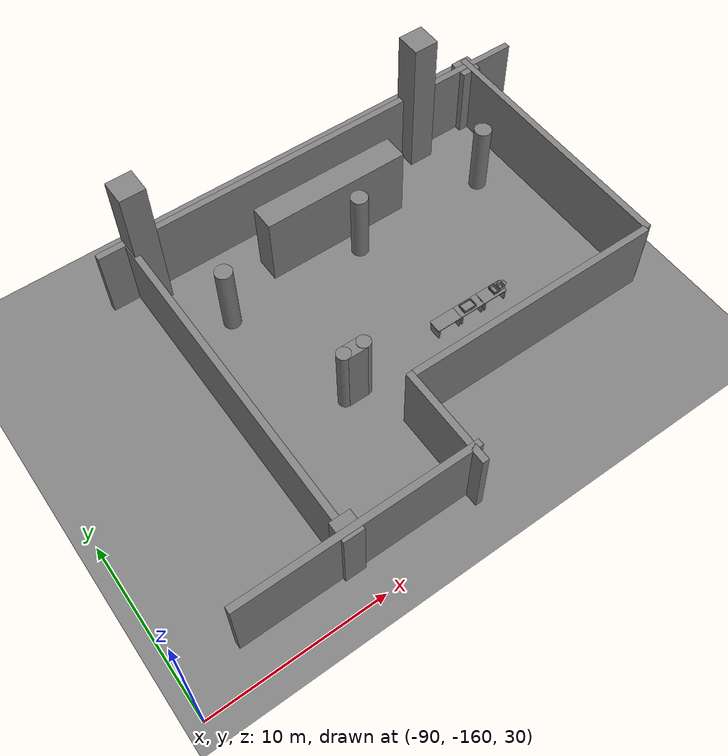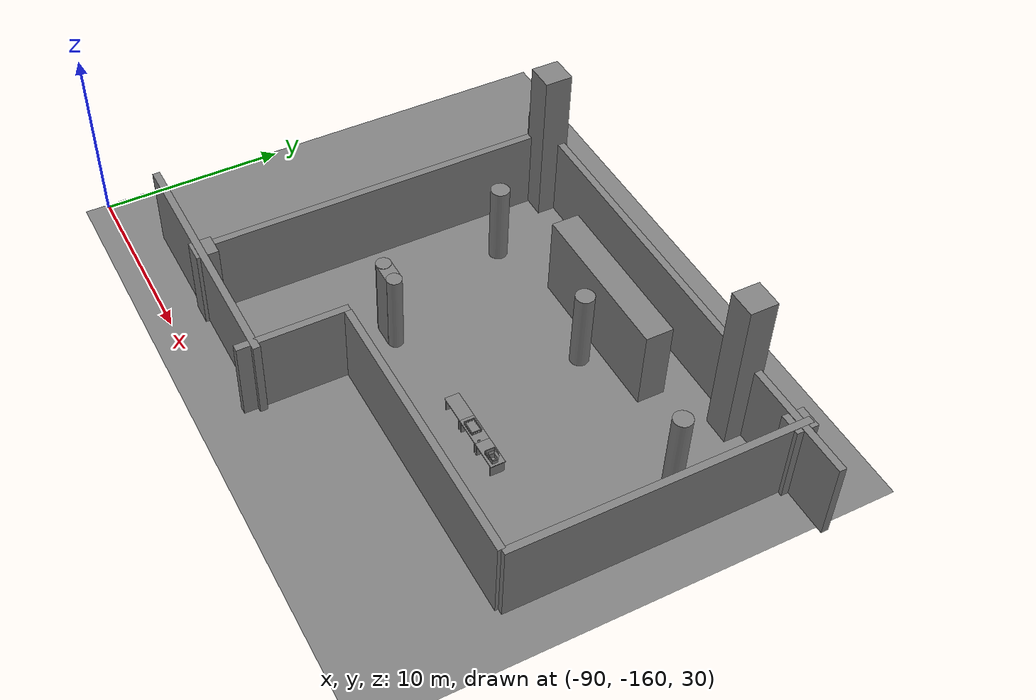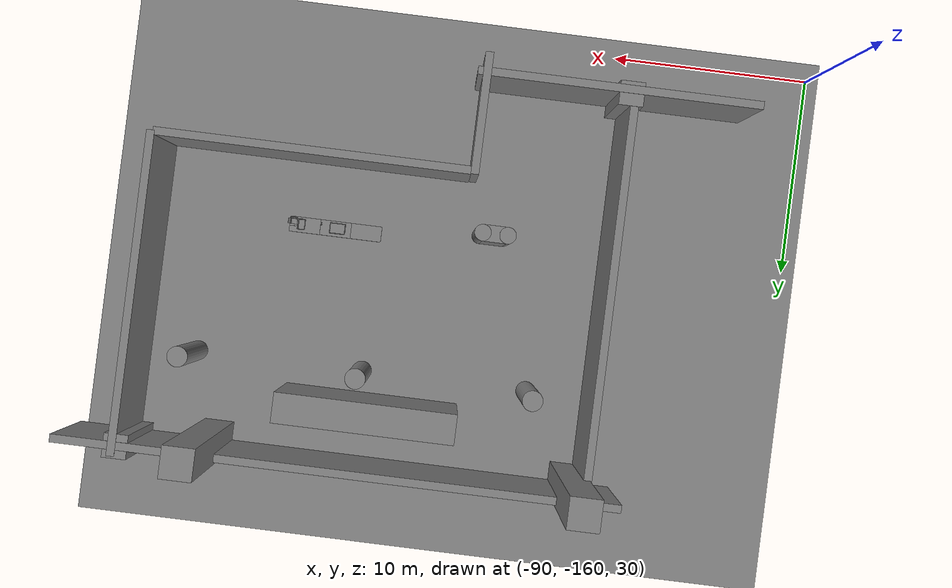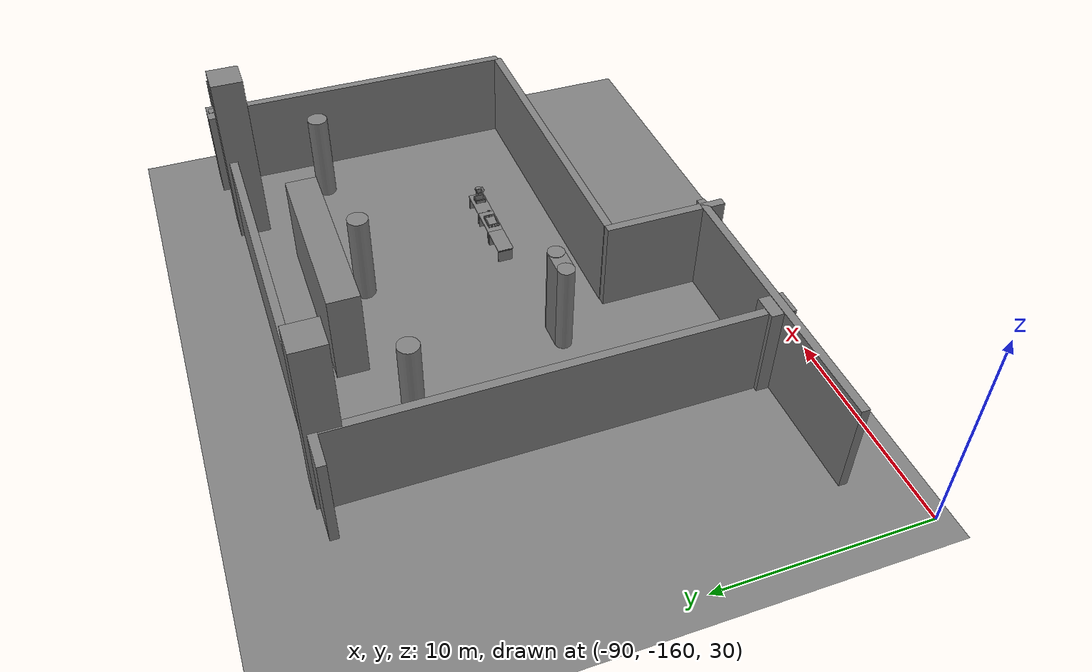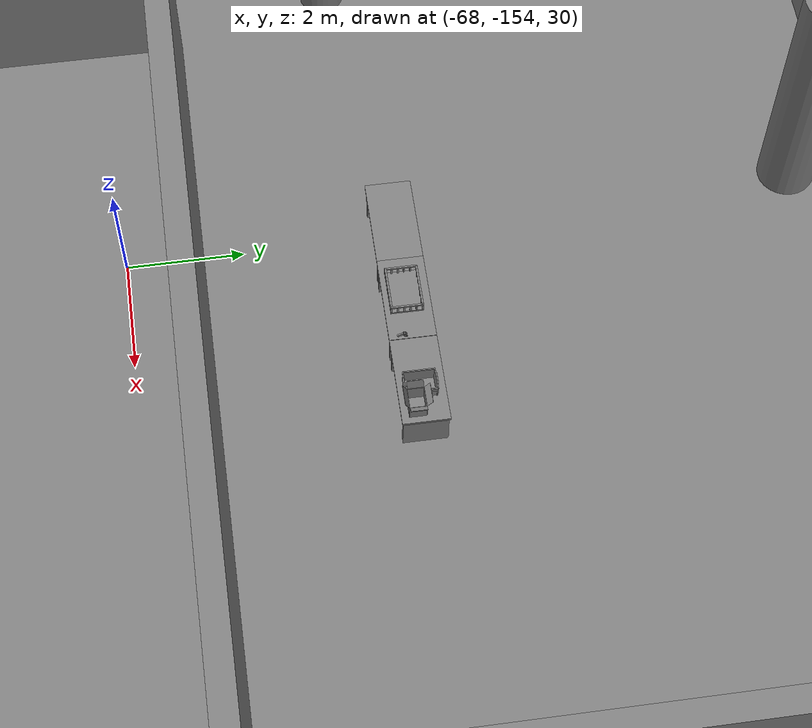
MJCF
<mujoco>
    <option gravity="0.000000000 0.000000000 -9.810000420" timestep="0.0049999999" integrator="implicitfast" density="1.225" viscosity="1.8000001e-05" noslip_iterations="10" iterations="100" sdf_iterations="50">
        <flag multiccd="disable"/>
    </option>
    <size memory="1000M"/>
    <compiler coordinate="local"/>
    <worldbody>
        <light cutoff="30" pos="0 1 1" dir="0 -1 -2"/>
        <light cutoff="30" pos="0 -1 1" dir="0 1 -2"/>
        <body pos="-64.866622925 -149.383972168 30.183746338" euler="89.999992371 89.999946594 0.000000000" name="openloong_gripper_2f85_fix_base_usda_bluebox_01">
            <geom contype="1" conaffinity="1" density="1000" type="box" material="" rgba="0.500000000 0.500000000 0.500000000 1.000000000" solimp="0.899999976 0.949999988 0.001000000" friction="1.000000000 0.005000000 0.000100000" solref="0.020000000 1.000000000" margin="0" condim="3" group="0" pos="0.276596069 0.187225342 0.000061035" quat="0.707107008 0.000077501 0.707106471 0.000077456" size="0.100000001 0.057999998 0.010000000" name="openloong_gripper_2f85_fix_base_usda_geom_4C8A9F81_D53C_4253_A86D_A51FE58609E5"/>
            <geom contype="1" conaffinity="1" density="1000" type="box" material="" rgba="0.500000000 0.500000000 0.500000000 1.000000000" solimp="0.899999976 0.949999988 0.001000000" friction="1.000000000 0.005000000 0.000100000" solref="0.020000000 1.000000000" margin="0" condim="3" group="0" pos="0.000000000 0.002883911 0.000000000" quat="1.000000000 0.000000000 0.000000000 0.000000000" size="0.254000008 0.003000000 0.172000006" name="openloong_gripper_2f85_fix_base_usda_geom_FA449A3E_7C81_44BC_A5B4_1AC3D94C5661"/>
            <geom contype="1" conaffinity="1" density="1000" type="box" material="" rgba="0.500000000 0.500000000 0.500000000 1.000000000" solimp="0.899999976 0.949999988 0.001000000" friction="1.000000000 0.005000000 0.000100000" solref="0.020000000 1.000000000" margin="0" condim="3" group="0" pos="0.000015259 0.124874115 0.173477173" quat="0.999796450 0.020176515 -0.000000015 0.000000030" size="0.259999990 0.119999997 0.007000000" name="openloong_gripper_2f85_fix_base_usda_geom_949F3E04_088C_4F17_B584_E83BF5275B4D"/>
            <geom contype="1" conaffinity="1" density="1000" type="box" material="" rgba="0.500000000 0.500000000 0.500000000 1.000000000" solimp="0.899999976 0.949999988 0.001000000" friction="1.000000000 0.005000000 0.000100000" solref="0.020000000 1.000000000" margin="0" condim="3" group="0" pos="0.000015259 0.124874115 -0.173477173" quat="0.999796450 -0.020176545 -0.000000015 0.000000000" size="0.259999990 0.119999997 0.007000000" name="openloong_gripper_2f85_fix_base_usda_geom_CD2CBDFC_A5AE_41DF_9291_7ABBE9171F49"/>
            <geom contype="1" conaffinity="1" density="1000" type="box" material="" rgba="0.500000000 0.500000000 0.500000000 1.000000000" solimp="0.899999976 0.949999988 0.001000000" friction="1.000000000 0.005000000 0.000100000" solref="0.020000000 1.000000000" margin="0" condim="3" group="0" pos="0.000015259 0.214012146 0.188980103" quat="0.999913096 0.013176724 0.000000015 0.000000000" size="0.259999990 0.029999999 0.012500000" name="openloong_gripper_2f85_fix_base_usda_geom_37F90AF2_A393_4356_973C_CF9FF52B4533"/>
            <geom contype="1" conaffinity="1" density="1000" type="box" material="" rgba="0.500000000 0.500000000 0.500000000 1.000000000" solimp="0.899999976 0.949999988 0.001000000" friction="1.000000000 0.005000000 0.000100000" solref="0.020000000 1.000000000" margin="0" condim="3" group="0" pos="-0.258346558 0.125289917 0.001876831" quat="0.702796996 -0.020792052 0.710783184 0.020769238" size="0.189999998 0.119999997 0.009000000" name="openloong_gripper_2f85_fix_base_usda_geom_67F28B11_2B8D_435A_AF58_6655376E8C4B"/>
            <geom contype="1" conaffinity="1" density="1000" type="box" material="" rgba="0.500000000 0.500000000 0.500000000 1.000000000" solimp="0.899999976 0.949999988 0.001000000" friction="1.000000000 0.005000000 0.000100000" solref="0.020000000 1.000000000" margin="0" condim="3" group="0" pos="0.000015259 0.214012146 -0.188980103" quat="0.999913096 -0.013176769 0.000000030 0.000000015" size="0.259999990 0.029999999 0.012500000" name="openloong_gripper_2f85_fix_base_usda_geom_3F5F7D08_1E6E_4A9E_95A3_BCE9E391F3A0"/>
            <geom contype="1" conaffinity="1" density="1000" type="box" material="" rgba="0.500000000 0.500000000 0.500000000 1.000000000" solimp="0.899999976 0.949999988 0.001000000" friction="1.000000000 0.005000000 0.000100000" solref="0.020000000 1.000000000" margin="0" condim="3" group="0" pos="-0.276596069 0.187225342 0.000061035" quat="0.707106650 0.000077441 0.707106709 0.000077456" size="0.100000001 0.057999998 0.010000000" name="openloong_gripper_2f85_fix_base_usda_geom_8523A11B_5381_4876_8A5E_C30389F47441"/>
            <geom contype="1" conaffinity="1" density="1000" type="box" material="" rgba="0.500000000 0.500000000 0.500000000 1.000000000" solimp="0.899999976 0.949999988 0.001000000" friction="1.000000000 0.005000000 0.000100000" solref="0.020000000 1.000000000" margin="0" condim="3" group="0" pos="0.258346558 0.125289917 0.001876831" quat="0.702851534 0.018856451 0.710823834 -0.019329429" size="0.189999998 0.119999997 0.009000000" name="openloong_gripper_2f85_fix_base_usda_geom_EFF69961_562E_402D_96B9_7259E67C5CB3"/>
            <freejoint name="openloong_gripper_2f85_fix_base_usda_bluebox_01_joint"/>
            <site size="0.005000000 0.005000000 0.005000000" rgba="0.500000000 0.500000000 0.500000000 1.000000000" pos="0.000000000 0.000000000 0.000000000" quat="0.999961913 0.008726534 0.000000000 0.000000000" group="0" type="sphere" name="openloong_gripper_2f85_fix_base_usda_bluebox_01site"/>
        </body>
        <body pos="-64.496299744 -149.491867065 30.235729218" euler="0.000000000 0.000000000 89.999946594" name="openloong_gripper_2f85_fix_base_usda_cardboardbox_01">
            <geom contype="1" conaffinity="1" density="1000" type="box" material="" rgba="0.500000000 0.500000000 0.500000000 1.000000000" solimp="0.899999976 0.949999988 0.001000000" friction="1.000000000 0.005000000 0.000100000" solref="0.020000000 1.000000000" margin="0" condim="3" group="0" pos="-0.003166199 -0.004086494 0.005052090" quat="1.000000000 0.000000000 0.000000000 0.000000000" size="0.142499998 0.177500010 0.005000000" name="openloong_gripper_2f85_fix_base_usda_geom_19803F77_3F98_4053_A917_C8C7CB608998"/>
            <geom contype="1" conaffinity="1" density="1000" type="box" material="" rgba="0.500000000 0.500000000 0.500000000 1.000000000" solimp="0.899999976 0.949999988 0.001000000" friction="1.000000000 0.005000000 0.000100000" solref="0.020000000 1.000000000" margin="0" condim="3" group="0" pos="-0.003166199 0.170316696 0.150570869" quat="1.000000000 0.000000000 0.000000000 0.000000000" size="0.142499998 0.005000000 0.149999991" name="openloong_gripper_2f85_fix_base_usda_geom_37E33005_E8E9_4975_8592_ABD713D045D6"/>
            <geom contype="1" conaffinity="1" density="1000" type="box" material="" rgba="0.500000000 0.500000000 0.500000000 1.000000000" solimp="0.899999976 0.949999988 0.001000000" friction="1.000000000 0.005000000 0.000100000" solref="0.020000000 1.000000000" margin="0" condim="3" group="0" pos="-0.147399902 -0.005307198 0.150570869" quat="1.000000000 0.000000000 0.000000000 0.000000000" size="0.005000000 0.177500010 0.149999991" name="openloong_gripper_2f85_fix_base_usda_geom_87D6290C_38E5_4BF5_9B2B_FEEBF7AD2773"/>
            <geom contype="1" conaffinity="1" density="1000" type="box" material="" rgba="0.500000000 0.500000000 0.500000000 1.000000000" solimp="0.899999976 0.949999988 0.001000000" friction="1.000000000 0.005000000 0.000100000" solref="0.020000000 1.000000000" margin="0" condim="3" group="0" pos="0.140275955 -0.005307198 0.150570869" quat="1.000000000 0.000000000 0.000000000 0.000000000" size="0.005000000 0.177500010 0.149999991" name="openloong_gripper_2f85_fix_base_usda_geom_57AB2C95_FC2E_4CA8_B913_CBA56820FB46"/>
            <geom contype="1" conaffinity="1" density="1000" type="box" material="" rgba="0.500000000 0.500000000 0.500000000 1.000000000" solimp="0.899999976 0.949999988 0.001000000" friction="1.000000000 0.005000000 0.000100000" solref="0.020000000 1.000000000" margin="0" condim="3" group="0" pos="-0.003166199 -0.181550980 0.150570869" quat="1.000000000 0.000000000 0.000000000 0.000000000" size="0.142499998 0.005000000 0.149999991" name="openloong_gripper_2f85_fix_base_usda_geom_141D40E4_2599_4931_B9F7_27B78343A139"/>
            <freejoint name="openloong_gripper_2f85_fix_base_usda_cardboardbox_01_joint"/>
            <site size="0.005000000 0.005000000 0.005000000" rgba="0.500000000 0.500000000 0.500000000 1.000000000" pos="0.000000000 0.000000000 0.000000000" quat="0.999961913 0.008726535 0.000000000 0.000000000" group="0" type="sphere" name="openloong_gripper_2f85_fix_base_usda_site_2133FF2F_AB4A_4D67_8812_94EA156B1614"/>
            <body pos="0.139160156 -0.004048347 0.301930904" euler="-179.999954224 49.383502960 179.999954224" name="openloong_gripper_2f85_fix_base_usda_A1_006">
                <geom contype="1" conaffinity="1" density="1000" type="box" material="" rgba="0.500000000 0.500000000 0.500000000 1.000000000" solimp="0.899999976 0.949999988 0.001000000" friction="1.000000000 0.005000000 0.000100000" solref="0.020000000 1.000000000" margin="0" condim="3" group="0" pos="-0.071587563 0.000009537 0.001745224" quat="0.999999881 0.000000000 0.000000000 0.000000000" size="0.071249999 0.179999992 0.002500000" name="openloong_gripper_2f85_fix_base_usda_geom_3475FBE2_D11F_4D34_AE08_B3191A70BFA7"/>
                <joint armature="0" stiffness="0.07" damping="0.0099999998" axis="0.000000 1.000000 0.000000" type="hinge" name="openloong_gripper_2f85_fix_base_usda_A1_006"/>
            </body>
            <body pos="-0.145902634 -0.004086494 0.301938057" euler="-180.000000000 -60.000011444 -180.000000000" name="openloong_gripper_2f85_fix_base_usda_A2_006">
                <geom contype="1" conaffinity="1" density="1000" type="box" material="" rgba="0.500000000 0.500000000 0.500000000 1.000000000" solimp="0.899999976 0.949999988 0.001000000" friction="1.000000000 0.005000000 0.000100000" solref="0.020000000 1.000000000" margin="0" condim="3" group="0" pos="0.071268082 0.000009537 0.002717972" quat="0.000002921 0.000000000 -0.000000030 0.999999881" size="0.071249999 0.179999992 0.002500000" name="openloong_gripper_2f85_fix_base_usda_geom_4657ECBA_884C_4B17_8A2F_132F7C44C244"/>
                <joint armature="0" stiffness="0.07" damping="0.0099999998" axis="0.000000 1.000000 0.000000" type="hinge" name="openloong_gripper_2f85_fix_base_usda_A2_006"/>
            </body>
            <body pos="-0.003385544 0.175991058 0.301930904" euler="-125.858116150 -0.000004561 0.000002331" name="openloong_gripper_2f85_fix_base_usda_B2_006">
                <geom contype="1" conaffinity="1" density="1000" type="box" material="" rgba="0.500000000 0.500000000 0.500000000 1.000000000" solimp="0.899999976 0.949999988 0.001000000" friction="1.000000000 0.005000000 0.000100000" solref="0.020000000 1.000000000" margin="0" condim="3" group="0" pos="0.000009537 -0.070939064 -0.002470016" quat="0.999614120 0.027776197 -0.000000015 0.000000030" size="0.137500003 0.064999998 0.005000000" name="openloong_gripper_2f85_fix_base_usda_geom_39AB5D5A_46ED_4273_9B67_1BF7458438EF"/>
                <joint armature="0" stiffness="0.07" damping="0.0099999998" axis="1.000000 0.000000 0.000000" type="hinge" name="openloong_gripper_2f85_fix_base_usda_B2_006"/>
            </body>
            <body pos="-0.003385544 -0.184140205 0.301938057" euler="147.805557251 0.000000000 0.000000000" name="openloong_gripper_2f85_fix_base_usda_B1_006">
                <geom contype="1" conaffinity="1" density="1000" type="box" material="" rgba="0.500000000 0.500000000 0.500000000 1.000000000" solimp="0.899999976 0.949999988 0.001000000" friction="1.000000000 0.005000000 0.000100000" solref="0.020000000 1.000000000" margin="0" condim="3" group="0" pos="-0.000028610 0.070202351 -0.002703667" quat="0.999614179 -0.027776167 0.000000000 0.000000000" size="0.137500003 0.064999998 0.005000000" name="openloong_gripper_2f85_fix_base_usda_geom_EC7D1599_E2DF_4810_AC34_86CABE5B6DCF"/>
                <joint armature="0" stiffness="0.07" damping="0.0099999998" axis="1.000000 0.000000 0.000000" type="hinge" name="openloong_gripper_2f85_fix_base_usda_B1_006"/>
            </body>
        </body>
        <body pos="-65.882858276 -149.481979370 30.229999542" euler="-64.487716675 0.000000000 0.000000000" name="openloong_gripper_2f85_fix_base_usda_Barcode">
            <geom contype="1" conaffinity="1" density="1000" type="box" material="" rgba="0.500000000 0.500000000 0.500000000 1.000000000" solimp="0.899999976 0.949999988 0.001000000" friction="1.000000000 0.005000000 0.000100000" solref="0.020000000 1.000000000" margin="0" condim="3" group="0" pos="0.000000000 0.013038635 0.001419067" quat="0.000000000 0.000000000 0.000000000 1.000000119" size="0.034000002 0.010000000 0.017999999" name="openloong_gripper_2f85_fix_base_usda_geom_D14FA1F7_6810_4CEC_B42E_72C00C83BBEF"/>
            <geom contype="1" conaffinity="1" density="1000" type="box" material="" rgba="0.500000000 0.500000000 0.500000000 1.000000000" solimp="0.899999976 0.949999988 0.001000000" friction="1.000000000 0.005000000 0.000100000" solref="0.020000000 1.000000000" margin="0" condim="3" group="0" pos="0.000000000 -0.035301208 -0.007095337" quat="0.000000000 0.000000000 -0.043619365 0.999048233" size="0.028999999 0.010000000 0.020000000" name="openloong_gripper_2f85_fix_base_usda_geom_0907B54B_9C5B_45FF_98E8_5D468C823B98"/>
            <geom contype="1" conaffinity="1" density="1000" type="box" material="" rgba="0.500000000 0.500000000 0.500000000 1.000000000" solimp="0.899999976 0.949999988 0.001000000" friction="1.000000000 0.005000000 0.000100000" solref="0.020000000 1.000000000" margin="0" condim="3" group="0" pos="0.000000000 -0.043411255 -0.011749268" quat="0.922262907 0.386563420 0.000000000 0.000000000" size="0.026000001 0.010000000 0.020000000" name="openloong_gripper_2f85_fix_base_usda_geom_C4567482_4105_4C3E_9C7D_F6534937ED2E"/>
            <geom contype="1" conaffinity="1" density="1000" type="box" material="" rgba="0.500000000 0.500000000 0.500000000 1.000000000" solimp="0.899999976 0.949999988 0.001000000" friction="1.000000000 0.005000000 0.000100000" solref="0.020000000 1.000000000" margin="0" condim="3" group="0" pos="0.000000000 -0.016967773 -0.031860352" quat="0.000000000 0.000000000 0.000000000 1.000000119" size="0.008000000 0.010000000 0.013000000" name="openloong_gripper_2f85_fix_base_usda_geom_4FB5A664_1DE3_48D4_A730_17364606FBAA"/>
            <geom contype="1" conaffinity="1" density="1000" type="box" material="" rgba="0.500000000 0.500000000 0.500000000 1.000000000" solimp="0.899999976 0.949999988 0.001000000" friction="1.000000000 0.005000000 0.000100000" solref="0.020000000 1.000000000" margin="0" condim="3" group="0" pos="0.000000000 -0.001869202 0.000312805" quat="0.953716993 0.300705761 0.000000000 0.000000000" size="0.032000002 0.010000000 0.018999999" name="openloong_gripper_2f85_fix_base_usda_geom_6676B0B3_670A_438B_934B_2EB6B7E583B0"/>
            <geom contype="1" conaffinity="1" density="1000" type="box" material="" rgba="0.500000000 0.500000000 0.500000000 1.000000000" solimp="0.899999976 0.949999988 0.001000000" friction="1.000000000 0.005000000 0.000100000" solref="0.020000000 1.000000000" margin="0" condim="3" group="0" pos="0.000000000 -0.019531250 -0.003173828" quat="0.953716993 0.300705761 0.000000000 0.000000000" size="0.030999999 0.010000000 0.020000000" name="openloong_gripper_2f85_fix_base_usda_geom_BD074233_1155_4C7B_882F_424E9D7BAA46"/>
            <geom contype="1" conaffinity="1" density="1000" type="box" material="" rgba="0.500000000 0.500000000 0.500000000 1.000000000" solimp="0.899999976 0.949999988 0.001000000" friction="1.000000000 0.005000000 0.000100000" solref="0.020000000 1.000000000" margin="0" condim="3" group="0" pos="0.000000000 -0.035301208 -0.007095337" quat="0.953716993 0.300705761 0.000000000 0.000000000" size="0.028999999 0.010000000 0.020000000" name="openloong_gripper_2f85_fix_base_usda_geom_B9DF298B_05C4_427D_A903_7DE9DACD27AA"/>
            <geom contype="1" conaffinity="1" density="1000" type="box" material="" rgba="0.500000000 0.500000000 0.500000000 1.000000000" solimp="0.899999976 0.949999988 0.001000000" friction="1.000000000 0.005000000 0.000100000" solref="0.020000000 1.000000000" margin="0" condim="3" group="0" pos="0.000000000 -0.042617798 -0.071121216" quat="0.000000000 0.000000000 0.000000000 1.000000119" size="0.013000000 0.021000000 0.059999999" name="openloong_gripper_2f85_fix_base_usda_geom_896C86A3_A9EA_48B5_82F2_BEF4F765AB4D"/>
            <freejoint name="openloong_gripper_2f85_fix_base_usda_Barcode_joint"/>
            <site size="0.005000000 0.005000000 0.005000000" rgba="0.500000000 0.500000000 0.500000000 1.000000000" pos="0.000000000 0.000000000 0.000000000" quat="1.000000000 0.000000000 0.000000000 0.000000000" group="0" type="sphere" name="openloong_gripper_2f85_fix_base_usda_Barcode_site"/>
        </body>
        <body pos="-66.745018005 -149.392349243 30.184000015" euler="0.000000000 0.000000000 89.999946594" name="[22329633777324]_Basket_01">
            <geom contype="1" conaffinity="1" density="1000" type="box" material="" rgba="0.500000000 0.500000000 0.500000000 1.000000000" solimp="0.899999976 0.949999988 0.001000000" friction="1.000000000 0.005000000 0.000100000" solref="0.020000000 1.000000000" margin="0" condim="3" group="0" pos="-0.052425385 0.389207840 0.089787483" quat="0.707107008 0.000000000 0.000000000 0.707106411" size="0.014249999 0.014249999 0.059999999" name="[22329633777324]_geom_3AD4E60B_AB87_4420_A8B6_E06FB99E3E4F"/>
            <geom contype="1" conaffinity="1" density="1000" type="box" material="" rgba="0.500000000 0.500000000 0.500000000 1.000000000" solimp="0.899999976 0.949999988 0.001000000" friction="1.000000000 0.005000000 0.000100000" solref="0.020000000 1.000000000" margin="0" condim="3" group="0" pos="0.264015198 -0.133043289 0.089787483" quat="0.707107008 0.000000000 0.000000000 0.707106411" size="0.014249999 0.014249999 0.059999999" name="[22329633777324]_geom_D13B75DC_DFD7_4BD7_B372_3CBDE2117F73"/>
            <geom contype="1" conaffinity="1" density="1000" type="box" material="" rgba="0.500000000 0.500000000 0.500000000 1.000000000" solimp="0.899999976 0.949999988 0.001000000" friction="1.000000000 0.005000000 0.000100000" solref="0.020000000 1.000000000" margin="0" condim="3" group="0" pos="-0.264015198 -0.265548706 0.089793205" quat="0.707107008 0.000000000 0.000000000 0.707106411" size="0.014249999 0.014249999 0.059999999" name="[22329633777324]_geom_4F33857A_2510_4F51_A2B9_D78DCDA8FFDC"/>
            <geom contype="1" conaffinity="1" density="1000" type="box" material="" rgba="0.500000000 0.500000000 0.500000000 1.000000000" solimp="0.899999976 0.949999988 0.001000000" friction="1.000000000 0.005000000 0.000100000" solref="0.020000000 1.000000000" margin="0" condim="3" group="0" pos="-0.160263062 -0.389322281 0.089793205" quat="0.707107008 0.000000000 0.000000000 0.707106411" size="0.014249999 0.014249999 0.059999999" name="[22329633777324]_geom_8F4F9681_AB83_4CE4_98A9_BA51806ECFB0"/>
            <geom contype="1" conaffinity="1" density="1000" type="box" material="" rgba="0.500000000 0.500000000 0.500000000 1.000000000" solimp="0.899999976 0.949999988 0.001000000" friction="1.000000000 0.005000000 0.000100000" solref="0.020000000 1.000000000" margin="0" condim="3" group="0" pos="0.162265778 -0.389322281 0.089787483" quat="0.707107008 0.000000000 0.000000000 0.707106411" size="0.014249999 0.014249999 0.059999999" name="[22329633777324]_geom_E881DA9C_F7FA_423D_8192_7D164CBDAB12"/>
            <geom contype="1" conaffinity="1" density="1000" type="box" material="" rgba="0.500000000 0.500000000 0.500000000 1.000000000" solimp="0.899999976 0.949999988 0.001000000" friction="1.000000000 0.005000000 0.000100000" solref="0.020000000 1.000000000" margin="0" condim="3" group="0" pos="0.264015198 0.389207840 0.089787483" quat="0.707107008 0.000000000 0.000000000 0.707106411" size="0.014249999 0.014249999 0.059999999" name="[22329633777324]_geom_68F230CF_2DFC_4E18_83B4_F9A6E0A03559"/>
            <geom contype="1" conaffinity="1" density="1000" type="box" material="" rgba="0.500000000 0.500000000 0.500000000 1.000000000" solimp="0.899999976 0.949999988 0.001000000" friction="1.000000000 0.005000000 0.000100000" solref="0.020000000 1.000000000" margin="0" condim="3" group="0" pos="-0.264015198 -0.133043289 0.089793205" quat="0.707107008 0.000000000 0.000000000 0.707106411" size="0.014249999 0.014249999 0.059999999" name="[22329633777324]_geom_D733270B_D57B_4F83_8BA6_5FEC3A127227"/>
            <geom contype="1" conaffinity="1" density="1000" type="box" material="" rgba="0.500000000 0.500000000 0.500000000 1.000000000" solimp="0.899999976 0.949999988 0.001000000" friction="1.000000000 0.005000000 0.000100000" solref="0.020000000 1.000000000" margin="0" condim="3" group="0" pos="-0.264026642 0.269256592 0.089793205" quat="0.707107008 0.000000000 0.000000000 0.707106411" size="0.014249999 0.014249999 0.059999999" name="[22329633777324]_geom_F4E99ED4_3CA0_4EAB_AE77_A77D617D7AC3"/>
            <geom contype="1" conaffinity="1" density="1000" type="box" material="" rgba="0.500000000 0.500000000 0.500000000 1.000000000" solimp="0.899999976 0.949999988 0.001000000" friction="1.000000000 0.005000000 0.000100000" solref="0.020000000 1.000000000" margin="0" condim="3" group="0" pos="0.054462433 0.389207840 0.089787483" quat="0.707107008 0.000000000 0.000000000 0.707106411" size="0.014249999 0.014249999 0.059999999" name="[22329633777324]_geom_E6733DC0_B312_4CA3_A00C_63DDE61ACA7A"/>
            <geom contype="1" conaffinity="1" density="1000" type="box" material="" rgba="0.500000000 0.500000000 0.500000000 1.000000000" solimp="0.899999976 0.949999988 0.001000000" friction="1.000000000 0.005000000 0.000100000" solref="0.020000000 1.000000000" margin="0" condim="3" group="0" pos="0.054462433 -0.389322281 0.089787483" quat="0.707107008 0.000000000 0.000000000 0.707106411" size="0.014249999 0.014249999 0.059999999" name="[22329633777324]_geom_62E011ED_EF34_4C37_BC88_5CA315E03F6E"/>
            <geom contype="1" conaffinity="1" density="1000" type="box" material="" rgba="0.500000000 0.500000000 0.500000000 1.000000000" solimp="0.899999976 0.949999988 0.001000000" friction="1.000000000 0.005000000 0.000100000" solref="0.020000000 1.000000000" margin="0" condim="3" group="0" pos="0.264015198 0.269256592 0.089793205" quat="0.707107008 0.000000000 0.000000000 0.707106411" size="0.014249999 0.014249999 0.059999999" name="[22329633777324]_geom_B714A408_1997_4E12_B5FF_85CCD1F7DEBB"/>
            <geom contype="1" conaffinity="1" density="1000" type="box" material="" rgba="0.500000000 0.500000000 0.500000000 1.000000000" solimp="0.899999976 0.949999988 0.001000000" friction="1.000000000 0.005000000 0.000100000" solref="0.020000000 1.000000000" margin="0" condim="3" group="0" pos="0.264015198 -0.389322281 0.089787483" quat="0.707107008 0.000000000 0.000000000 0.707106411" size="0.014249999 0.014249999 0.059999999" name="[22329633777324]_geom_14D67183_D2F1_443C_A5A3_6134EFE1402E"/>
            <geom contype="1" conaffinity="1" density="1000" type="box" material="" rgba="0.500000000 0.500000000 0.500000000 1.000000000" solimp="0.899999976 0.949999988 0.001000000" friction="1.000000000 0.005000000 0.000100000" solref="0.020000000 1.000000000" margin="0" condim="3" group="0" pos="0.000000000 0.000000000 0.015998840" quat="0.707107008 0.000000000 0.000000000 0.707106411" size="0.403499991 0.279000014 0.015750000" name="[22329633777324]_geom_2159CED3_B146_4CAE_BC24_38E2812BC573"/>
            <geom contype="1" conaffinity="1" density="1000" type="box" material="" rgba="0.500000000 0.500000000 0.500000000 1.000000000" solimp="0.899999976 0.949999988 0.001000000" friction="1.000000000 0.005000000 0.000100000" solref="0.020000000 1.000000000" margin="0" condim="3" group="0" pos="0.000000000 -0.389476776 0.163619041" quat="0.707107008 0.000000000 0.000000000 0.707106411" size="0.015000000 0.277500004 0.015750000" name="[22329633777324]_geom_2D59739C_62B8_4111_9941_CE522D7A7B55"/>
            <geom contype="1" conaffinity="1" density="1000" type="box" material="" rgba="0.500000000 0.500000000 0.500000000 1.000000000" solimp="0.899999976 0.949999988 0.001000000" friction="1.000000000 0.005000000 0.000100000" solref="0.020000000 1.000000000" margin="0" condim="3" group="0" pos="0.162265778 0.389207840 0.089787483" quat="0.707107008 0.000000000 0.000000000 0.707106411" size="0.014249999 0.014249999 0.059999999" name="[22329633777324]_geom_F0860B09_DCF9_4298_93EB_17881008EEC6"/>
            <geom contype="1" conaffinity="1" density="1000" type="box" material="" rgba="0.500000000 0.500000000 0.500000000 1.000000000" solimp="0.899999976 0.949999988 0.001000000" friction="1.000000000 0.005000000 0.000100000" solref="0.020000000 1.000000000" margin="0" condim="3" group="0" pos="0.000000000 0.389471054 0.163619041" quat="0.707107008 0.000000000 0.000000000 0.707106411" size="0.015000000 0.277500004 0.015750000" name="[22329633777324]_geom_EAF025F2_F562_49DD_A602_8DEBBFE3AF66"/>
            <geom contype="1" conaffinity="1" density="1000" type="box" material="" rgba="0.500000000 0.500000000 0.500000000 1.000000000" solimp="0.899999976 0.949999988 0.001000000" friction="1.000000000 0.005000000 0.000100000" solref="0.020000000 1.000000000" margin="0" condim="3" group="0" pos="-0.263511658 0.000000000 0.163619041" quat="0.707107008 0.000000000 0.000000000 0.707106411" size="0.403499991 0.015000000 0.015750000" name="[22329633777324]_geom_2E044EAE_DEEB_4CF0_AF57_009B08EBEE0D"/>
            <geom contype="1" conaffinity="1" density="1000" type="box" material="" rgba="0.500000000 0.500000000 0.500000000 1.000000000" solimp="0.899999976 0.949999988 0.001000000" friction="1.000000000 0.005000000 0.000100000" solref="0.020000000 1.000000000" margin="0" condim="3" group="0" pos="-0.264015198 0.141334534 0.089793205" quat="0.707107008 0.000000000 0.000000000 0.707106411" size="0.014249999 0.014249999 0.059999999" name="[22329633777324]_geom_78AA6CAD_AAE6_4FE9_8990_D8CE96156511"/>
            <geom contype="1" conaffinity="1" density="1000" type="box" material="" rgba="0.500000000 0.500000000 0.500000000 1.000000000" solimp="0.899999976 0.949999988 0.001000000" friction="1.000000000 0.005000000 0.000100000" solref="0.020000000 1.000000000" margin="0" condim="3" group="0" pos="0.264015198 -0.265548706 0.089787483" quat="0.707107008 0.000000000 0.000000000 0.707106411" size="0.014249999 0.014249999 0.059999999" name="[22329633777324]_geom_392DA23E_30C5_44D6_A7ED_86A65476C9E8"/>
            <geom contype="1" conaffinity="1" density="1000" type="box" material="" rgba="0.500000000 0.500000000 0.500000000 1.000000000" solimp="0.899999976 0.949999988 0.001000000" friction="1.000000000 0.005000000 0.000100000" solref="0.020000000 1.000000000" margin="0" condim="3" group="0" pos="-0.160263062 0.389207840 0.089787483" quat="0.707107008 0.000000000 0.000000000 0.707106411" size="0.014249999 0.014249999 0.059999999" name="[22329633777324]_geom_AE10BA55_0E20_4505_988A_D92EE085577C"/>
            <geom contype="1" conaffinity="1" density="1000" type="box" material="" rgba="0.500000000 0.500000000 0.500000000 1.000000000" solimp="0.899999976 0.949999988 0.001000000" friction="1.000000000 0.005000000 0.000100000" solref="0.020000000 1.000000000" margin="0" condim="3" group="0" pos="-0.052425385 -0.389322281 0.089787483" quat="0.707107008 0.000000000 0.000000000 0.707106411" size="0.014249999 0.014249999 0.059999999" name="[22329633777324]_geom_975CE984_9408_4E67_B27A_D1C3C0151417"/>
            <geom contype="1" conaffinity="1" density="1000" type="box" material="" rgba="0.500000000 0.500000000 0.500000000 1.000000000" solimp="0.899999976 0.949999988 0.001000000" friction="1.000000000 0.005000000 0.000100000" solref="0.020000000 1.000000000" margin="0" condim="3" group="0" pos="-0.264026642 -0.389322281 0.089793205" quat="0.707107008 0.000000000 0.000000000 0.707106411" size="0.014249999 0.014249999 0.059999999" name="[22329633777324]_geom_4CA66516_7471_47D8_B9FC_DEE2E1A425F7"/>
            <geom contype="1" conaffinity="1" density="1000" type="box" material="" rgba="0.500000000 0.500000000 0.500000000 1.000000000" solimp="0.899999976 0.949999988 0.001000000" friction="1.000000000 0.005000000 0.000100000" solref="0.020000000 1.000000000" margin="0" condim="3" group="0" pos="0.264015198 0.141334534 0.089787483" quat="0.707107008 0.000000000 0.000000000 0.707106411" size="0.014249999 0.014249999 0.059999999" name="[22329633777324]_geom_A2A6CE23_A979_43E3_9B11_F70114BC9A8A"/>
            <geom contype="1" conaffinity="1" density="1000" type="box" material="" rgba="0.500000000 0.500000000 0.500000000 1.000000000" solimp="0.899999976 0.949999988 0.001000000" friction="1.000000000 0.005000000 0.000100000" solref="0.020000000 1.000000000" margin="0" condim="3" group="0" pos="-0.264015198 0.389207840 0.089793205" quat="0.707107008 0.000000000 0.000000000 0.707106411" size="0.014249999 0.014249999 0.059999999" name="[22329633777324]_geom_3D1BEC56_1326_4973_945B_6EF12D417DD3"/>
            <geom contype="1" conaffinity="1" density="1000" type="box" material="" rgba="0.500000000 0.500000000 0.500000000 1.000000000" solimp="0.899999976 0.949999988 0.001000000" friction="1.000000000 0.005000000 0.000100000" solref="0.020000000 1.000000000" margin="0" condim="3" group="0" pos="0.264015198 0.004480362 0.089787483" quat="0.707107008 0.000000000 0.000000000 0.707106411" size="0.014249999 0.014249999 0.059999999" name="[22329633777324]_geom_8AA2E9D6_81CC_4401_A3E1_7C01E290B5F0"/>
            <geom contype="1" conaffinity="1" density="1000" type="box" material="" rgba="0.500000000 0.500000000 0.500000000 1.000000000" solimp="0.899999976 0.949999988 0.001000000" friction="1.000000000 0.005000000 0.000100000" solref="0.020000000 1.000000000" margin="0" condim="3" group="0" pos="0.263694763 -0.000011444 0.163619041" quat="0.707107008 0.000000000 0.000000000 0.707106411" size="0.403499991 0.015000000 0.015750000" name="[22329633777324]_geom_8528F738_8D95_424A_8781_C86D37EDFB62"/>
            <geom contype="1" conaffinity="1" density="1000" type="box" material="" rgba="0.500000000 0.500000000 0.500000000 1.000000000" solimp="0.899999976 0.949999988 0.001000000" friction="1.000000000 0.005000000 0.000100000" solref="0.020000000 1.000000000" margin="0" condim="3" group="0" pos="-0.264015198 0.004480362 0.089793205" quat="0.707107008 0.000000000 0.000000000 0.707106411" size="0.014249999 0.014249999 0.059999999" name="[22329633777324]_geom_A7ACFC9A_21A3_40C7_91F2_99537FDFFF37"/>
            <freejoint name="[22329633777324]_joint_85DC4888_28F8_437C_93B9_D191DCD5E9A2"/>
        </body>
        <body pos="0.000000000 0.000000000 0.000000000" euler="0.000000000 0.000000000 0.000000000" name="Static Objects_Static Objects">
            <geom contype="1" conaffinity="1" density="1000" type="box" material="" rgba="0.500000000 0.500000000 0.500000000 1.000000000" solimp="0.899999976 0.949999988 0.001000000" friction="1.000000000 0.005000000 0.000100000" solref="0.020000000 1.000000000" margin="0" condim="3" group="0" pos="-67.544113159 -149.365814209 29.727830887" quat="0.500000417 0.499999970 0.499999553 0.499999970" size="0.381000012 0.319999993 0.041000001" name="Static Objects_geom_B6C7A1F5_3FC0_481D_9B9D_30EF739ABE3A"/>
            <geom contype="1" conaffinity="1" density="1000" type="box" material="" rgba="0.500000000 0.500000000 0.500000000 1.000000000" solimp="0.899999976 0.949999988 0.001000000" friction="1.000000000 0.005000000 0.000100000" solref="0.020000000 1.000000000" margin="0" condim="3" group="0" pos="-68.239501953 -149.365814209 30.086868286" quat="0.500000417 0.499999970 0.499999553 0.499999970" size="0.370999992 0.039500002 0.745000005" name="Static Objects_geom_2996A5B9_B92E_45CC_9B47_E5AC90001AA5"/>
            <geom contype="1" conaffinity="1" density="1000" type="box" material="" rgba="0.500000000 0.500000000 0.500000000 1.000000000" solimp="0.899999976 0.949999988 0.001000000" friction="1.000000000 0.005000000 0.000100000" solref="0.020000000 1.000000000" margin="0" condim="3" group="0" pos="-68.239501953 -149.365814209 30.147235870" quat="0.500000417 0.499999970 0.499999553 0.499999970" size="0.400000006 0.022000000 0.800000012" name="Static Objects_geom_D3809F09_BA72_43E6_A58B_10B6326FC442"/>
            <geom contype="1" conaffinity="1" density="1000" type="box" material="" rgba="0.500000000 0.500000000 0.500000000 1.000000000" solimp="0.899999976 0.949999988 0.001000000" friction="1.000000000 0.005000000 0.000100000" solref="0.020000000 1.000000000" margin="0" condim="3" group="0" pos="-68.934890747 -149.365814209 29.727830887" quat="0.500000417 0.499999970 0.499999553 0.499999970" size="0.381000012 0.319999993 0.041000001" name="Static Objects_geom_B6497968_DCE9_4662_AEDD_C2140E02F2E9"/>
            <geom contype="1" conaffinity="1" density="1000" type="box" material="" rgba="0.500000000 0.500000000 0.500000000 1.000000000" solimp="0.899999976 0.949999988 0.001000000" friction="1.000000000 0.005000000 0.000100000" solref="0.020000000 1.000000000" margin="0" condim="3" group="0" pos="-68.239501953 -149.365814209 29.561563492" quat="0.500000417 0.499999970 0.499999553 0.499999970" size="0.020000000 0.022000000 0.660000026" name="Static Objects_geom_A88B7C5A_7CC9_4BAF_87E7_A1A158DB373A"/>
            <geom contype="1" conaffinity="1" density="1000" type="box" material="" rgba="0.500000000 0.500000000 0.500000000 1.000000000" solimp="0.899999976 0.949999988 0.001000000" friction="1.000000000 0.005000000 0.000100000" solref="0.020000000 1.000000000" margin="0" condim="3" group="0" pos="-65.945671082 -149.365814209 29.727830887" quat="0.500000417 0.499999970 0.499999553 0.499999970" size="0.381000012 0.319999993 0.041000001" name="Static Objects_geom_8B0CE7EF_98A9_453A_B44B_BEB426CADA6D"/>
            <geom contype="1" conaffinity="1" density="1000" type="box" material="" rgba="0.500000000 0.500000000 0.500000000 1.000000000" solimp="0.899999976 0.949999988 0.001000000" friction="1.000000000 0.005000000 0.000100000" solref="0.020000000 1.000000000" margin="0" condim="3" group="0" pos="-66.641059875 -149.365814209 30.086868286" quat="0.500000417 0.499999970 0.499999553 0.499999970" size="0.370999992 0.039500002 0.745000005" name="Static Objects_geom_D67D6382_147A_4640_8C66_FC91EC782A92"/>
            <geom contype="1" conaffinity="1" density="1000" type="box" material="" rgba="0.500000000 0.500000000 0.500000000 1.000000000" solimp="0.899999976 0.949999988 0.001000000" friction="1.000000000 0.005000000 0.000100000" solref="0.020000000 1.000000000" margin="0" condim="3" group="0" pos="-66.641059875 -149.365814209 30.147235870" quat="0.500000417 0.499999970 0.499999553 0.499999970" size="0.400000006 0.022000000 0.800000012" name="Static Objects_geom_52D90F79_34BE_4A19_9A3B_A3D10CB9F1FF"/>
            <geom contype="1" conaffinity="1" density="1000" type="box" material="" rgba="0.500000000 0.500000000 0.500000000 1.000000000" solimp="0.899999976 0.949999988 0.001000000" friction="1.000000000 0.005000000 0.000100000" solref="0.020000000 1.000000000" margin="0" condim="3" group="0" pos="-67.336448669 -149.365814209 29.727830887" quat="0.500000417 0.499999970 0.499999553 0.499999970" size="0.381000012 0.319999993 0.041000001" name="Static Objects_geom_9C5DDBDB_51DA_4E74_A009_D2DC21780DF9"/>
            <geom contype="1" conaffinity="1" density="1000" type="box" material="" rgba="0.500000000 0.500000000 0.500000000 1.000000000" solimp="0.899999976 0.949999988 0.001000000" friction="1.000000000 0.005000000 0.000100000" solref="0.020000000 1.000000000" margin="0" condim="3" group="0" pos="-66.641059875 -149.365814209 29.561563492" quat="0.500000417 0.499999970 0.499999553 0.499999970" size="0.020000000 0.022000000 0.660000026" name="Static Objects_geom_DAB5C79C_1A44_4C26_A7C1_EC572879271E"/>
            <geom contype="1" conaffinity="1" density="1000" type="box" material="" rgba="0.500000000 0.500000000 0.500000000 1.000000000" solimp="0.899999976 0.949999988 0.001000000" friction="1.000000000 0.005000000 0.000100000" solref="0.020000000 1.000000000" margin="0" condim="3" group="0" pos="-64.338577271 -149.365814209 29.727830887" quat="0.500000417 0.499999970 0.499999553 0.499999970" size="0.381000012 0.319999993 0.041000001" name="Static Objects_geom_AB547048_ACF0_496E_B9E5_1F2A3A67A0F8"/>
            <geom contype="1" conaffinity="1" density="1000" type="box" material="" rgba="0.500000000 0.500000000 0.500000000 1.000000000" solimp="0.899999976 0.949999988 0.001000000" friction="1.000000000 0.005000000 0.000100000" solref="0.020000000 1.000000000" margin="0" condim="3" group="0" pos="-65.033966064 -149.365814209 30.086868286" quat="0.500000417 0.499999970 0.499999553 0.499999970" size="0.370999992 0.039500002 0.745000005" name="Static Objects_geom_997F8DAB_0508_4021_BB7C_FEBF4EBA3C67"/>
            <geom contype="1" conaffinity="1" density="1000" type="box" material="" rgba="0.500000000 0.500000000 0.500000000 1.000000000" solimp="0.899999976 0.949999988 0.001000000" friction="1.000000000 0.005000000 0.000100000" solref="0.020000000 1.000000000" margin="0" condim="3" group="0" pos="-65.033966064 -149.365814209 30.147235870" quat="0.500000417 0.499999970 0.499999553 0.499999970" size="0.400000006 0.022000000 0.800000012" name="Static Objects_geom_F147B67D_CD18_4B36_AD08_B6505780C4C8"/>
            <geom contype="1" conaffinity="1" density="1000" type="box" material="" rgba="0.500000000 0.500000000 0.500000000 1.000000000" solimp="0.899999976 0.949999988 0.001000000" friction="1.000000000 0.005000000 0.000100000" solref="0.020000000 1.000000000" margin="0" condim="3" group="0" pos="-65.729354858 -149.365814209 29.727830887" quat="0.500000417 0.499999970 0.499999553 0.499999970" size="0.381000012 0.319999993 0.041000001" name="Static Objects_geom_9FDBC74F_D2B3_4707_B98E_169C099D07E1"/>
            <geom contype="1" conaffinity="1" density="1000" type="box" material="" rgba="0.500000000 0.500000000 0.500000000 1.000000000" solimp="0.899999976 0.949999988 0.001000000" friction="1.000000000 0.005000000 0.000100000" solref="0.020000000 1.000000000" margin="0" condim="3" group="0" pos="-65.033966064 -149.365814209 29.561563492" quat="0.500000417 0.499999970 0.499999553 0.499999970" size="0.020000000 0.022000000 0.660000026" name="Static Objects_geom_6B0707DE_3C97_4219_8CA4_1DA4E43BF9C7"/>
            <geom contype="1" conaffinity="1" density="1000" type="box" material="" rgba="0.500000000 0.500000000 0.500000000 1.000000000" solimp="0.899999976 0.949999988 0.001000000" friction="1.000000000 0.005000000 0.000100000" solref="0.020000000 1.000000000" margin="0" condim="3" group="0" pos="-61.754566193 -137.853729248 33.906845093" quat="0.707107067 0.000000000 0.000000000 0.707106471" size="0.759999990 0.759999990 4.500000000" name="Static Objects_geom_27CB5D07_BA0B_49D8_9B9A_FBFA33D48335"/>
            <geom contype="1" conaffinity="1" density="1000" type="box" material="" rgba="0.500000000 0.500000000 0.500000000 1.000000000" solimp="0.899999976 0.949999988 0.001000000" friction="1.000000000 0.005000000 0.000100000" solref="0.020000000 1.000000000" margin="0" condim="3" group="0" pos="-57.511135101 -144.927108765 31.707921982" quat="1.000000000 0.000000000 0.000000000 0.000000000" size="0.200000003 8.000000000 2.299999952" name="Static Objects_geom_85383C3D_724B_4E45_A8E6_A7F4886F873E"/>
            <geom contype="1" conaffinity="1" density="1000" type="box" material="" rgba="0.500000000 0.500000000 0.500000000 1.000000000" solimp="0.899999976 0.949999988 0.001000000" friction="1.000000000 0.005000000 0.000100000" solref="0.020000000 1.000000000" margin="0" condim="3" group="0" pos="-80.517646790 -157.574050903 31.688196182" quat="0.707107067 0.000000000 0.000000000 0.707106471" size="0.600000024 0.600000024 2.299999952" name="Static Objects_geom_2BEDC946_ED91_4A5A_A115_036D1CD4603B"/>
            <geom contype="1" conaffinity="1" density="1000" type="box" material="" rgba="0.500000000 0.500000000 0.500000000 1.000000000" solimp="0.899999976 0.949999988 0.001000000" friction="1.000000000 0.005000000 0.000100000" solref="0.020000000 1.000000000" margin="0" condim="3" group="0" pos="-80.711044312 -147.414932251 31.666158676" quat="1.000000000 0.000000000 0.000000000 0.000000000" size="0.200000003 10.000000000 2.299999952" name="Static Objects_geom_67D1A842_2512_40F1_A54A_CD445F543F9D"/>
            <geom contype="1" conaffinity="1" density="1000" type="box" material="" rgba="0.500000000 0.500000000 0.500000000 1.000000000" solimp="0.899999976 0.949999988 0.001000000" friction="1.000000000 0.005000000 0.000100000" solref="0.020000000 1.000000000" margin="0" condim="3" group="0" pos="-57.687217712 -137.434692383 31.688196182" quat="0.707107067 0.000000000 0.000000000 0.707106471" size="0.600000024 0.600000024 2.299999952" name="Static Objects_geom_E2479CB3_2F96_4347_9058_0AFF1338B5B9"/>
            <geom contype="1" conaffinity="1" density="1000" type="box" material="" rgba="0.500000000 0.500000000 0.500000000 1.000000000" solimp="0.899999976 0.949999988 0.001000000" friction="1.000000000 0.005000000 0.000100000" solref="0.020000000 1.000000000" margin="0" condim="3" group="0" pos="-69.537033081 -140.263229370 31.714921951" quat="0.707107067 0.000000000 0.000000000 0.707106471" size="0.759999990 4.500000000 2.299999952" name="Static Objects_geom_ACB00AFB_F78E_4BE3_A781_99CE3CF0C747"/>
            <geom contype="1" conaffinity="1" density="1000" type="box" material="" rgba="0.500000000 0.500000000 0.500000000 1.000000000" solimp="0.899999976 0.949999988 0.001000000" friction="1.000000000 0.005000000 0.000100000" solref="0.020000000 1.000000000" margin="0" condim="3" group="0" pos="-80.073638916 -137.853713989 33.906845093" quat="0.707107067 0.000000000 0.000000000 0.707106471" size="0.759999990 0.759999990 4.500000000" name="Static Objects_geom_2D59D055_7961_48B1_BE4D_BAA98E036E66"/>
            <geom contype="1" conaffinity="1" density="1000" type="box" material="" rgba="0.500000000 0.500000000 0.500000000 1.000000000" solimp="0.899999976 0.949999988 0.001000000" friction="1.000000000 0.005000000 0.000100000" solref="0.020000000 1.000000000" margin="0" condim="3" group="0" pos="-73.406707764 -155.734664917 31.707921982" quat="1.000000000 0.000000000 0.000000000 0.000000000" size="0.200000003 3.000000000 2.299999952" name="Static Objects_geom_2738DA30_5632_4D93_B932_52A3200761B9"/>
            <geom contype="1" conaffinity="1" density="1000" type="box" material="" rgba="0.500000000 0.500000000 0.500000000 1.000000000" solimp="0.899999976 0.949999988 0.001000000" friction="1.000000000 0.005000000 0.000100000" solref="0.020000000 1.000000000" margin="0" condim="3" group="0" pos="-68.497543335 -137.448257446 31.707921982" quat="0.707107067 0.000000000 0.000000000 0.707106471" size="0.200000003 14.000000000 2.299999952" name="Static Objects_geom_403C997A_A48F_4F36_9003_C3619BA0C92C"/>
            <geom contype="1" conaffinity="1" density="1000" type="cylinder" material="" rgba="0.500000000 0.500000000 0.500000000 1.000000000" solimp="0.899999976 0.949999988 0.001000000" friction="1.000000000 0.005000000 0.000100000" solref="0.020000000 1.000000000" margin="0" condim="3" group="0" pos="-68.868522644 -142.134506226 31.711090088" quat="0.707107067 0.000000000 0.000000000 0.707106471" size="0.509999990 2.299999952 1.000000000" name="Static Objects_geom_1CF2A1EF_9E42_4592_B8BF_6BC623F7C127"/>
            <geom contype="1" conaffinity="1" density="1000" type="plane" material="" rgba="0.500000000 0.500000000 0.500000000 1.000000000" solimp="0.899999976 0.949999988 0.001000000" friction="1.000000000 0.005000000 0.000100000" solref="0.020000000 1.000000000" margin="0" condim="3" group="0" pos="-72.873703003 -147.131927490 29.409669876" quat="1.000000000 0.000000000 0.000000000 0.000000000" size="18.000000000 14.000000000 1.000000000" name="Static Objects_geom_E4C62D0C_0265_4705_AB74_6B1835ED51C6"/>
            <geom contype="1" conaffinity="1" density="1000" type="box" material="" rgba="0.500000000 0.500000000 0.500000000 1.000000000" solimp="0.899999976 0.949999988 0.001000000" friction="1.000000000 0.005000000 0.000100000" solref="0.020000000 1.000000000" margin="0" condim="3" group="0" pos="-79.943580627 -157.782272339 31.707921982" quat="0.707107067 0.000000000 0.000000000 0.707106471" size="0.200000003 7.000000000 2.299999952" name="Static Objects_geom_4037A3B5_4AD6_4F4F_B422_EB8CDC259F22"/>
            <geom contype="1" conaffinity="1" density="1000" type="box" material="" rgba="0.500000000 0.500000000 0.500000000 1.000000000" solimp="0.899999976 0.949999988 0.001000000" friction="1.000000000 0.005000000 0.000100000" solref="0.020000000 1.000000000" margin="0" condim="3" group="0" pos="-65.421028137 -152.903442383 31.707921982" quat="0.707107067 0.000000000 0.000000000 0.707106471" size="0.200000003 7.800000191 2.299999952" name="Static Objects_geom_336A0F57_37E9_47B7_8CE8_9381E41D6605"/>
            <geom contype="1" conaffinity="1" density="1000" type="box" material="" rgba="0.500000000 0.500000000 0.500000000 1.000000000" solimp="0.899999976 0.949999988 0.001000000" friction="1.000000000 0.005000000 0.000100000" solref="0.020000000 1.000000000" margin="0" condim="3" group="0" pos="-74.776908875 -149.964416504 31.688196182" quat="1.000000000 0.000000000 0.000000000 0.000000000" size="0.600000024 0.409999996 2.299999952" name="Static Objects_geom_955B0A66_49C6_446D_A64D_C20C6F91AA15"/>
            <geom contype="1" conaffinity="1" density="1000" type="cylinder" material="" rgba="0.500000000 0.500000000 0.500000000 1.000000000" solimp="0.899999976 0.949999988 0.001000000" friction="1.000000000 0.005000000 0.000100000" solref="0.020000000 1.000000000" margin="0" condim="3" group="0" pos="-60.161884308 -142.134506226 31.711090088" quat="0.707107067 0.000000000 0.000000000 0.707106471" size="0.509999990 2.299999952 1.000000000" name="Static Objects_geom_B7F45E74_35CD_497F_8284_35D65A7CF518"/>
            <geom contype="1" conaffinity="1" density="1000" type="cylinder" material="" rgba="0.500000000 0.500000000 0.500000000 1.000000000" solimp="0.899999976 0.949999988 0.001000000" friction="1.000000000 0.005000000 0.000100000" solref="0.020000000 1.000000000" margin="0" condim="3" group="0" pos="-75.382453918 -149.963455200 31.711090088" quat="0.707107067 0.000000000 0.000000000 0.707106471" size="0.409999996 2.299999952 1.000000000" name="Static Objects_geom_20EA0042_744D_4DFF_A2F4_3915FE1DB1DA"/>
            <geom contype="1" conaffinity="1" density="1000" type="cylinder" material="" rgba="0.500000000 0.500000000 0.500000000 1.000000000" solimp="0.899999976 0.949999988 0.001000000" friction="1.000000000 0.005000000 0.000100000" solref="0.020000000 1.000000000" margin="0" condim="3" group="0" pos="-74.154960632 -149.963455200 31.711090088" quat="0.707107067 0.000000000 0.000000000 0.707106471" size="0.409999996 2.299999952 1.000000000" name="Static Objects_geom_9CF357BC_8E40_4CCE_8557_B4FAD23FF3D2"/>
            <geom contype="1" conaffinity="1" density="1000" type="cylinder" material="" rgba="0.500000000 0.500000000 0.500000000 1.000000000" solimp="0.899999976 0.949999988 0.001000000" friction="1.000000000 0.005000000 0.000100000" solref="0.020000000 1.000000000" margin="0" condim="3" group="0" pos="-77.566612244 -142.134506226 31.711090088" quat="0.707107067 0.000000000 0.000000000 0.707106471" size="0.509999990 2.299999952 1.000000000" name="Static Objects_geom_5B300282_8657_4B7A_8579_A422EF9B0399"/>
        </body>
        <body pos="-66.291030884 -149.869689941 29.018842697" euler="0.000000000 0.000000000 89.999946594" mocap="true" name="openloong_gripper_2f85_fix_base_usda_leftHandMocap"/>
        <body pos="-66.291030884 -149.869689941 29.018842697" euler="0.000000000 0.000000000 89.999946594" mocap="true" name="openloong_gripper_2f85_fix_base_usda_rightHandMocap"/>
        <body pos="-66.291030884 -149.869689941 30.218843460" euler="0.000000000 0.000000000 89.999946594" name="openloong_gripper_2f85_fix_base_usda_base_link">
            <geom contype="1" conaffinity="1" density="1000" type="mesh" material="" rgba="0.783999979 0.783999979 0.783999979 1.000000000" solimp="0.899999976 0.949999988 0.001000000" friction="1.000000000 0.005000000 0.000100000" solref="0.020000000 1.000000000" margin="0" condim="3" group="3" mesh="base_link" pos="0.000000000 0.000000000 0.000000000" quat="1.000000000 0.000000000 0.000000000 0.000000000" size="1.000000000 1.000000000 1.000000000" name="openloong_gripper_2f85_fix_base_usda__geom_7_A9A9343B_9749_4A07_84A6_C23ADB9D1BA7"/>
            <site size="0.005000000 0.005000000 0.005000000" rgba="0.500000000 0.500000000 0.500000000 1.000000000" pos="0.000000000 0.000000000 0.000000000" quat="1.000000000 0.000000000 0.000000000 0.000000000" group="0" type="sphere" name="openloong_gripper_2f85_fix_base_usda_imu"/>
            <inertial mass="22.447001" pos="-0.005664100 -0.001336700 0.238289997" diaginertia="0.374352545 0.277180195 0.220617250" quat="0.999247074 0.035235517 -0.015086859 0.006023135"/>
            <body pos="0.000000000 0.000000000 0.299997330" euler="0.000000000 0.000000000 0.000000000" name="openloong_gripper_2f85_fix_base_usda_dummy_body">
                <geom contype="1" conaffinity="1" density="1000" type="sphere" material="" rgba="0.783999979 0.783999979 0.783999979 1.000000000" solimp="0.899999976 0.949999988 0.001000000" friction="1.000000000 0.005000000 0.000100000" solref="0.020000000 1.000000000" margin="0" condim="3" group="3" pos="0.000000000 0.000000000 0.000000000" quat="1.000000000 0.000000000 0.000000000 0.000000000" size="0.010000000 0.000000000 0.000000000" name="openloong_gripper_2f85_fix_base_usda__geom_8_338FAF13_B3D5_4290_8C0D_F89F53EFAC89"/>
                <joint armature="0.0099999998" stiffness="0" damping="0.1" axis="0.000000 0.000000 1.000000" type="hinge" name="openloong_gripper_2f85_fix_base_usda_dummy_joint"/>
                <site size="0.010000000 0.005000000 0.005000000" rgba="0.500000000 0.500000000 0.500000000 1.000000000" pos="0.000000000 0.000000000 0.000000000" quat="1.000000000 0.000000000 0.000000000 0.000000000" group="3" type="sphere" name="openloong_gripper_2f85_fix_base_usda_dummy_site"/>
            </body>
            <body pos="0.009002686 0.000000000 0.406400681" euler="0.000000000 0.000000000 0.000000000" name="openloong_gripper_2f85_fix_base_usda_Link_head_yaw">
                <geom contype="1" conaffinity="1" density="1000" type="mesh" material="" rgba="0.783999979 0.783999979 0.783999979 1.000000000" solimp="0.899999976 0.949999988 0.001000000" friction="1.000000000 0.005000000 0.000100000" solref="0.020000000 1.000000000" margin="0" condim="3" group="3" mesh="Link_head_yaw" pos="0.000000000 0.000000000 0.000000000" quat="1.000000000 0.000000000 0.000000000 0.000000000" size="1.000000000 1.000000000 1.000000000" name="openloong_gripper_2f85_fix_base_usda__geom_10_91C58055_3B3D_4661_94BB_45CE29C3FCD5"/>
                <inertial mass="0.84249002" pos="0.000000000 -0.002081400 0.044801001" diaginertia="0.000700588 0.000629000 0.000553812" quat="0.706933022 -0.015675601 0.015677100 0.706933022"/>
                <body pos="0.000000000 -0.034599304 0.048500061" euler="0.000000000 0.000000000 0.000000000" name="openloong_gripper_2f85_fix_base_usda_Link_head_pitch">
                    <geom contype="1" conaffinity="1" density="1000" type="mesh" material="" rgba="0.783999979 0.783999979 0.783999979 1.000000000" solimp="0.899999976 0.949999988 0.001000000" friction="1.000000000 0.005000000 0.000100000" solref="0.020000000 1.000000000" margin="0" condim="3" group="3" mesh="Link_head_pitch" pos="0.000000000 0.000000000 0.000000000" quat="1.000000000 0.000000000 0.000000000 0.000000000" size="1.000000000 1.000000000 1.000000000" name="openloong_gripper_2f85_fix_base_usda__geom_12_0E2D3B91_DA26_48D8_B2AA_9A67FFCB86DD"/>
                    <inertial mass="1.3943" pos="0.020569000 0.033004001 0.125000000" diaginertia="0.006381400 0.006289940 0.004481460" quat="0.973390222 0.008406822 0.228157058 0.019624906"/>
                    <body pos="0.000000000 0.029998779 0.000000000" euler="0.000000000 0.000000000 0.000000000" name="openloong_gripper_2f85_fix_base_usda_neck_center_body">
                        <site size="0.010000000 0.005000000 0.005000000" rgba="0.500000000 0.500000000 0.500000000 1.000000000" pos="0.000000000 0.000000000 0.000000000" quat="1.000000000 0.000000000 0.000000000 0.000000000" group="3" type="sphere" name="openloong_gripper_2f85_fix_base_usda_neck_center_site"/>
                        <body pos="0.020004272 0.000000000 0.149999619" euler="-0.000002229 39.998176575 -90.000205994" name="openloong_gripper_2f85_fix_base_usda_camera_head">
                            <site size="0.010000000 0.005000000 0.005000000" rgba="0.500000000 0.500000000 0.500000000 1.000000000" pos="0.000000000 0.000000000 0.000000000" quat="1.000000000 0.000000000 0.000000000 0.000000000" group="3" type="sphere" name="openloong_gripper_2f85_fix_base_usda_camera_head_site"/>
                        </body>
                    </body>
                </body>
            </body>
            <body pos="0.003997803 -0.161598206 0.392200470" euler="0.000000000 0.000000000 0.000000000" name="openloong_gripper_2f85_fix_base_usda_Link_arm_r_01">
                <geom contype="1" conaffinity="1" density="1000" type="mesh" material="" rgba="0.783999979 0.783999979 0.783999979 1.000000000" solimp="0.899999976 0.949999988 0.001000000" friction="1.000000000 0.005000000 0.000100000" solref="0.020000000 1.000000000" margin="0" condim="3" group="3" mesh="Link_arm_r_01" pos="0.000000000 0.000000000 0.000000000" quat="1.000000000 0.000000000 0.000000000 0.000000000" size="1.000000000 1.000000000 1.000000000" name="openloong_gripper_2f85_fix_base_usda__geom_14_904EBD2C_8DAE_4E65_A1C9_1505813CF17C"/>
                <joint armature="0.0099999998" stiffness="0" damping="1" axis="0.000000 -1.000000 0.000000" limited="true" range="-170.000015259 170.000015259" type="hinge" name="openloong_gripper_2f85_fix_base_usda_J_arm_r_01"/>
                <inertial mass="0.75641" pos="0.004494600 -0.038293999 -0.000001874" diaginertia="0.000842990 0.000803050 0.000587120" quat="-0.000163502 0.707098067 0.000812463 0.707115054"/>
                <body pos="-0.041992188 -0.041000366 0.000000000" euler="0.000000000 0.000000000 0.000000000" name="openloong_gripper_2f85_fix_base_usda_Link_arm_r_02">
                    <geom contype="1" conaffinity="1" density="1000" type="mesh" material="" rgba="0.783999979 0.783999979 0.783999979 1.000000000" solimp="0.899999976 0.949999988 0.001000000" friction="1.000000000 0.005000000 0.000100000" solref="0.020000000 1.000000000" margin="0" condim="3" group="3" mesh="Link_arm_r_02" pos="0.000000000 0.000000000 0.000000000" quat="1.000000000 0.000000000 0.000000000 0.000000000" size="1.000000000 1.000000000 1.000000000" name="openloong_gripper_2f85_fix_base_usda__geom_16_ADD8AA50_9F75_41D4_AFA0_FDF448DE2103"/>
                    <joint armature="0.0099999998" stiffness="0" damping="1" axis="-1.000000 0.000000 0.000000" limited="true" range="-105.000244141 105.000244141" type="hinge" name="openloong_gripper_2f85_fix_base_usda_J_arm_r_02"/>
                    <inertial mass="0.98500001" pos="0.041999999 -0.067430697 0.000000000" diaginertia="0.002262690 0.001730990 0.001154020" quat="0.500000000 0.500000000 -0.500000000 0.500000000"/>
                    <body pos="0.041992188 -0.122596741 0.000000000" euler="0.000000000 0.000000000 0.000000000" name="openloong_gripper_2f85_fix_base_usda_Link_arm_r_03">
                        <geom contype="1" conaffinity="1" density="1000" type="mesh" material="" rgba="0.783999979 0.783999979 0.783999979 1.000000000" solimp="0.899999976 0.949999988 0.001000000" friction="1.000000000 0.005000000 0.000100000" solref="0.020000000 1.000000000" margin="0" condim="3" group="3" mesh="Link_arm_r_03" pos="0.000000000 0.000000000 0.000000000" quat="1.000000000 0.000000000 0.000000000 0.000000000" size="1.000000000 1.000000000 1.000000000" name="openloong_gripper_2f85_fix_base_usda__geom_18_40EEF681_A81C_455F_BFBE_2D219BB4E27A"/>
                        <joint armature="0.0099999998" stiffness="0" damping="1" axis="0.000000 -1.000000 0.000000" limited="true" range="-170.000015259 170.000015259" type="hinge" name="openloong_gripper_2f85_fix_base_usda_J_arm_r_03"/>
                        <inertial mass="0.95899999" pos="-0.001413580 -0.164663002 0.020757901" diaginertia="0.002101340 0.002064590 0.000754802" quat="0.560480952 0.454391927 -0.443732947 0.531497955"/>
                        <body pos="0.035293579 -0.177406311 0.023998260" euler="0.000000000 0.000000000 0.000000000" name="openloong_gripper_2f85_fix_base_usda_Link_arm_r_04">
                            <geom contype="1" conaffinity="1" density="1000" type="mesh" material="" rgba="0.783999979 0.783999979 0.783999979 1.000000000" solimp="0.899999976 0.949999988 0.001000000" friction="1.000000000 0.005000000 0.000100000" solref="0.020000000 1.000000000" margin="0" condim="3" group="3" mesh="Link_arm_r_04" pos="0.000000000 0.000000000 0.000000000" quat="1.000000000 0.000000000 0.000000000 0.000000000" size="1.000000000 1.000000000 1.000000000" name="openloong_gripper_2f85_fix_base_usda__geom_20_BDE4AFEA_62B0_44C9_B4D6_579B1F127258"/>
                            <joint armature="0.0099999998" stiffness="0" damping="1" axis="-1.000000 0.000000 0.000000" limited="true" range="0.000000000 170.000015259" type="hinge" name="openloong_gripper_2f85_fix_base_usda_J_arm_r_04"/>
                            <inertial mass="0.60000002" pos="-0.038727000 -0.060766999 -0.021003000" diaginertia="0.001092610 0.000712422 0.000645102" quat="0.327701002 0.632602990 -0.467366993 0.523443997"/>
                            <body pos="-0.035293579 -0.103492737 -0.023998260" euler="0.000000000 0.000000000 0.000000000" name="openloong_gripper_2f85_fix_base_usda_Link_arm_r_05">
                                <geom contype="1" conaffinity="1" density="1000" type="mesh" material="" rgba="0.783999979 0.783999979 0.783999979 1.000000000" solimp="0.899999976 0.949999988 0.001000000" friction="1.000000000 0.005000000 0.000100000" solref="0.020000000 1.000000000" margin="0" condim="3" group="3" mesh="Link_arm_r_05" pos="0.000000000 0.000000000 0.000000000" quat="1.000000000 0.000000000 0.000000000 0.000000000" size="1.000000000 1.000000000 1.000000000" name="openloong_gripper_2f85_fix_base_usda__geom_22_2ABD7774_76A0_4967_9898_4F429E097C8C"/>
                                <joint armature="0.0099999998" stiffness="0" damping="1" axis="0.000000 -1.000000 0.000000" limited="true" range="-170.000015259 170.000015259" type="hinge" name="openloong_gripper_2f85_fix_base_usda_J_arm_r_05"/>
                                <inertial mass="0.68976003" pos="0.000032712 -0.068658002 -0.000111780" diaginertia="0.002522510 0.002411100 0.000448695" quat="0.707660973 0.706543028 -0.002603360 0.002470550"/>
                                <body pos="-0.026489258 -0.196502686 0.000000000" euler="0.000000000 0.000000000 0.000000000" name="openloong_gripper_2f85_fix_base_usda_Link_arm_r_06">
                                    <geom contype="1" conaffinity="1" density="1000" type="mesh" material="" rgba="0.783999979 0.783999979 0.783999979 1.000000000" solimp="0.899999976 0.949999988 0.001000000" friction="1.000000000 0.005000000 0.000100000" solref="0.020000000 1.000000000" margin="0" condim="3" group="3" mesh="Link_arm_r_06" pos="0.000000000 0.000000000 0.000000000" quat="1.000000000 0.000000000 0.000000000 0.000000000" size="1.000000000 1.000000000 1.000000000" name="openloong_gripper_2f85_fix_base_usda__geom_24_B94A7730_2B0A_4E2B_BB5E_9A8EECA689B5"/>
                                    <joint armature="0.0099999998" stiffness="0" damping="1" axis="1.000000 0.000000 0.000000" limited="true" range="-105.000244141 105.000244141" type="hinge" name="openloong_gripper_2f85_fix_base_usda_J_arm_r_06"/>
                                    <inertial mass="0.28" pos="0.026078001 -0.000000896 0.001663700" diaginertia="0.000156930 0.000145601 0.000104979" quat="0.707080841 0.001851080 0.001883810 0.707127810"/>
                                    <body pos="0.026489258 0.000000000 0.031799316" euler="0.000000000 0.000000000 0.000000000" name="openloong_gripper_2f85_fix_base_usda_Link_arm_r_07">
                                        <geom contype="1" conaffinity="1" density="1000" type="mesh" material="" rgba="0.783999979 0.783999979 0.783999979 1.000000000" solimp="0.899999976 0.949999988 0.001000000" friction="1.000000000 0.005000000 0.000100000" solref="0.020000000 1.000000000" margin="0" condim="3" group="3" mesh="Link_arm_r_07" pos="0.000000000 0.000000000 0.000000000" quat="1.000000000 0.000000000 0.000000000 0.000000000" size="1.000000000 1.000000000 1.000000000" name="openloong_gripper_2f85_fix_base_usda__geom_26_715EB579_380F_4F3E_B1F4_190BF0789984"/>
                                        <joint armature="0.0099999998" stiffness="0" damping="1" axis="0.000000 0.000000 1.000000" limited="true" range="-60.000133514 60.000133514" type="hinge" name="openloong_gripper_2f85_fix_base_usda_J_arm_r_07"/>
                                        <inertial mass="0.61353999" pos="-0.007859000 -0.158170000 -0.027736001" diaginertia="0.003037610 0.002570910 0.000729379" quat="0.427542925 0.443532884 -0.553093910 0.560867906"/>
                                        <body pos="0.000000000 0.286994934 -0.270000458" euler="150.000350952 -0.000001649 -0.000000442" name="openloong_gripper_2f85_fix_base_usda_camera_wrist_r">
                                            <site size="0.010000000 0.005000000 0.005000000" rgba="0.500000000 0.500000000 0.500000000 1.000000000" pos="0.000000000 0.000000000 0.000000000" quat="1.000000000 0.000000000 0.000000000 0.000000000" group="3" type="sphere" name="openloong_gripper_2f85_fix_base_usda_camera_wrist_r_site"/>
                                        </body>
                                        <body pos="0.000000000 -0.220008850 -0.033002853" euler="0.000000000 0.000000000 179.999969482" name="openloong_gripper_2f85_fix_base_usda_ee_center_body_r">
                                            <site size="0.010000000 0.005000000 0.005000000" rgba="0.500000000 0.500000000 0.500000000 1.000000000" pos="0.000000000 0.000000000 0.000000000" quat="1.000000000 0.000000000 0.000000000 0.000000000" group="3" type="sphere" name="openloong_gripper_2f85_fix_base_usda_ee_center_site_r"/>
                                        </body>
                                        <body pos="0.000000000 -0.066001892 -0.031000137" euler="89.999984741 0.000000000 180.000000000" name="openloong_gripper_2f85_fix_base_usda_zbr_base_link">
                                            <geom contype="1" conaffinity="1" density="1000" type="mesh" material="" rgba="0.783999979 0.783999979 0.783999979 1.000000000" solimp="0.899999976 0.949999988 0.001000000" friction="1.000000000 0.005000000 0.000100000" solref="0.020000000 1.000000000" margin="0" condim="3" group="3" mesh="base" pos="0.000000000 0.000003815 -0.000007629" quat="1.000000000 0.000000000 0.000000000 0.000000000" size="1.000000238 1.000000238 1.000000238" name="openloong_gripper_2f85_fix_base_usda__geom_30_7FF7DC9F_556F_4A3B_B94C_F6829D837DFB"/>
                                            <inertial mass="0.77744102" pos="0.000000000 -0.000027039 0.035467502" diaginertia="0.000260285 0.000225381 0.000152708" quat="0.999998808 -0.001528488 0.000000000 0.000000000"/>
                                            <body pos="-0.030609138 0.004745484 0.065696731" euler="-89.999984741 -0.000000000 0.000000000" name="openloong_gripper_2f85_fix_base_usda_r_left_driver">
                                                <geom contype="1" conaffinity="1" density="1000" type="mesh" material="" rgba="0.783999979 0.783999979 0.783999979 1.000000000" solimp="0.899999976 0.949999988 0.001000000" friction="1.000000000 0.005000000 0.000100000" solref="0.020000000 1.000000000" margin="0" condim="3" group="3" mesh="driver" pos="0.030609138 0.054901138 -0.004699708" quat="0.707106829 0.707106709 0.000000000 -0.000000000" size="1.000000238 1.000000238 1.000000238" name="openloong_gripper_2f85_fix_base_usda__geom_32_69B3BD20_7448_47C9_99A2_76FC506AC2EC"/>
                                                <joint armature="0.0049999999" stiffness="0" damping="0.1" axis="0.000000 0.000000 1.000000" limited="true" range="0.000000000 51.566200256" type="hinge" name="openloong_gripper_2f85_fix_base_usda_r_left_driver_joint"/>
                                                <inertial mass="0.0089956298" pos="0.000000000 0.017754700 0.001073140" diaginertia="0.000001724 0.000001609 0.000000322" quat="0.681301236 0.732003212 0.000000000 0.000000000"/>
                                                <body pos="-0.031402595 0.004524232 -0.010200503" euler="0.000000000 0.000000000 180.000000000" name="openloong_gripper_2f85_fix_base_usda_r_left_coupler">
                                                    <geom contype="1" conaffinity="1" density="1000" type="mesh" material="" rgba="0.783999979 0.783999979 0.783999979 1.000000000" solimp="0.899999976 0.949999988 0.001000000" friction="1.000000000 0.005000000 0.000100000" solref="0.020000000 1.000000000" margin="0" condim="3" group="3" mesh="coupler" pos="-0.062011734 -0.050354015 0.005500795" quat="0.707106829 -0.707106709 0.000000000 -0.000000000" size="1.000000238 1.000000238 1.000000238" name="openloong_gripper_2f85_fix_base_usda__geom_34_A2EBF1BC_F8A7_4685_8D68_D242FC1164F8"/>
                                                    <inertial mass="0.0140974" pos="0.000000000 0.003012090 0.023217499" diaginertia="0.000004162 0.000003522 0.000000888" quat="0.705635548 -0.045590367 0.045590367 0.705635548"/>
                                                </body>
                                            </body>
                                            <body pos="-0.012695315 -0.012001040 0.072212234" euler="-89.999984741 -0.000000000 0.000000000" name="openloong_gripper_2f85_fix_base_usda_r_left_spring_link">
                                                <geom contype="1" conaffinity="1" density="1000" type="mesh" material="" rgba="0.783999979 0.783999979 0.783999979 1.000000000" solimp="0.899999976 0.949999988 0.001000000" friction="1.000000000 0.005000000 0.000100000" solref="0.020000000 1.000000000" margin="0" condim="3" group="3" mesh="spring_link" pos="0.012695315 0.061416641 0.012050631" quat="0.707106829 0.707106709 0.000000000 -0.000000000" size="1.000000238 1.000000238 1.000000238" name="openloong_gripper_2f85_fix_base_usda__geom_36_8F7E87D5_978D_41A9_A4C7_EE02DFC4A626"/>
                                                <joint armature="0.001" stiffness="0.050000001" damping="0.00125" axis="0.000000 0.000000 1.000000" limited="true" range="-17.000000000 51.566200256" type="hinge" name="openloong_gripper_2f85_fix_base_usda_r_left_spring_link_joint"/>
                                                <inertial mass="0.0221642" pos="-0.000000009 0.018162400 0.021265799" diaginertia="0.000008969 0.000006717 0.000002639" quat="0.663403213 -0.244737089 0.244737089 0.663403213"/>
                                                <body pos="-0.038208015 -0.042503368 0.002950669" euler="180.000000000 0.000000000 -0.002185660" name="openloong_gripper_2f85_fix_base_usda_r_left_follower">
                                                    <geom contype="1" conaffinity="1" density="1000" type="mesh" material="" rgba="0.783999979 0.783999979 0.783999979 1.000000000" solimp="0.899999976 0.949999988 0.001000000" friction="1.000000000 0.005000000 0.000100000" solref="0.020000000 1.000000000" margin="0" condim="3" group="3" mesh="tongue" pos="0.050918590 -0.103920005 -0.009099962" quat="0.707106829 -0.707106709 0.000000030 0.000000030" size="1.000000238 1.000000238 1.000000238" name="openloong_gripper_2f85_fix_base_usda__geom_40_A7A57603_41CB_45E7_8F14_AFFCF2C3654F"/>
                                                    <geom contype="1" conaffinity="1" density="1000" type="mesh" material="" rgba="0.783999979 0.783999979 0.783999979 1.000000000" solimp="0.899999976 0.949999988 0.001000000" friction="1.000000000 0.005000000 0.000100000" solref="0.020000000 1.000000000" margin="0" condim="3" group="3" mesh="follower" pos="0.050918590 -0.103920005 -0.009099962" quat="0.707106829 -0.707106709 0.000000030 0.000000030" size="1.000000238 1.000000238 1.000000238" name="openloong_gripper_2f85_fix_base_usda__geom_39_93B60A2B_6D70_4BE3_A2C4_F0F0322B73C3"/>
                                                    <joint armature="0.001" stiffness="0" damping="0.1" axis="0.000000 0.000000 1.000000" limited="true" range="-49.999961853 51.566200256" type="hinge" name="openloong_gripper_2f85_fix_base_usda_r_left_follower"/>
                                                    <inertial mass="0.0125222" pos="0.000000000 -0.011046000 0.012478600" diaginertia="0.000002674 0.000002456 0.000000602" quat="0.986436546 0.164143041 0.000000000 0.000000000"/>
                                                    <body pos="-0.037765510 -0.103912376 -0.009099962" euler="-89.999984741 0.000000000 0.000004829" name="openloong_gripper_2f85_fix_base_usda_r_left_pad">
                                                        <geom contype="1" conaffinity="1" density="1000" type="box" material="" rgba="0.550000012 0.550000012 0.550000012 1.000000000" solimp="0.949999988 0.990000010 0.001000000" friction="0.699999988 0.005000000 0.000100000" solref="0.020000000 1.000000000" margin="0" condim="3" group="3" mass="1e-06" pos="0.043243419 0.000003815 0.119995147" quat="0.999999881 0.000000000 0.000000000 0.000000000" size="0.002000001 0.011000003 0.009375002" name="openloong_gripper_2f85_fix_base_usda_r_left_pad1_0ACBD83B_3F33_413A_A1F0_4530E4D550D0"/>
                                                        <geom contype="1" conaffinity="1" density="1000" type="box" material="" rgba="0.449999988 0.449999988 0.449999988 1.000000000" solimp="0.949999988 0.990000010 0.001000000" friction="0.600000024 0.005000000 0.000100000" solref="0.020000000 1.000000000" margin="0" condim="3" group="3" mass="1e-06" pos="0.043243419 0.000003815 0.138748199" quat="0.999999881 0.000000000 0.000000000 0.000000000" size="0.002000001 0.011000003 0.009375002" name="openloong_gripper_2f85_fix_base_usda_r_left_pad2_EC1D2E11_EF21_48BD_A5CE_623A006F8E0F"/>
                                                    </body>
                                                </body>
                                            </body>
                                            <body pos="0.030593880 -0.004753114 0.065696731" euler="89.999984741 0.000000000 180.000000000" name="openloong_gripper_2f85_fix_base_usda_r_right_driver">
                                                <geom contype="1" conaffinity="1" density="1000" type="mesh" material="" rgba="0.783999979 0.783999979 0.783999979 1.000000000" solimp="0.899999976 0.949999988 0.001000000" friction="1.000000000 0.005000000 0.000100000" solref="0.020000000 1.000000000" margin="0" condim="3" group="3" mesh="driver" pos="0.030593880 0.054901138 -0.004699708" quat="0.707106829 0.707106709 0.000000000 0.000000000" size="1.000000238 1.000000238 1.000000238" name="openloong_gripper_2f85_fix_base_usda__geom_42_448C79E0_7367_4D47_B4E7_4C70FD7943C3"/>
                                                <joint armature="0.0049999999" stiffness="0" damping="0.1" axis="0.000000 0.000000 1.000000" limited="true" range="0.000000000 51.566200256" type="hinge" name="openloong_gripper_2f85_fix_base_usda_r_right_driver_joint"/>
                                                <inertial mass="0.0089956298" pos="0.000000000 0.017754700 0.001073140" diaginertia="0.000001724 0.000001609 0.000000322" quat="0.681301236 0.732003212 0.000000000 0.000000000"/>
                                                <body pos="-0.031417854 0.004531861 -0.010202411" euler="0.000000000 0.000000000 180.000000000" name="openloong_gripper_2f85_fix_base_usda_r_right_coupler">
                                                    <geom contype="1" conaffinity="1" density="1000" type="mesh" material="" rgba="0.783999979 0.783999979 0.783999979 1.000000000" solimp="0.899999976 0.949999988 0.001000000" friction="1.000000000 0.005000000 0.000100000" solref="0.020000000 1.000000000" margin="0" condim="3" group="3" mesh="coupler" pos="-0.062042251 -0.050376903 0.005500795" quat="0.707106829 -0.707106709 0.000000000 0.000000000" size="1.000000238 1.000000238 1.000000238" name="openloong_gripper_2f85_fix_base_usda__geom_44_43D6A34E_216B_4DB5_B082_9FF2D8C56ABC"/>
                                                    <inertial mass="0.0140974" pos="0.000000000 0.003012090 0.023217499" diaginertia="0.000004162 0.000003522 0.000000888" quat="0.705635548 -0.045590367 0.045590367 0.705635548"/>
                                                </body>
                                            </body>
                                            <body pos="0.012695315 0.011997226 0.072219864" euler="89.999984741 0.000000000 180.000000000" name="openloong_gripper_2f85_fix_base_usda_r_right_spring_link">
                                                <geom contype="1" conaffinity="1" density="1000" type="mesh" material="" rgba="0.783999979 0.783999979 0.783999979 1.000000000" solimp="0.899999976 0.949999988 0.001000000" friction="1.000000000 0.005000000 0.000100000" solref="0.020000000 1.000000000" margin="0" condim="3" group="3" mesh="spring_link" pos="0.012695315 0.061424270 0.012048724" quat="0.707106829 0.707106709 0.000000000 0.000000000" size="1.000000238 1.000000238 1.000000238" name="openloong_gripper_2f85_fix_base_usda__geom_46_B6784DB6_D162_4650_ADF1_6C7876A68540"/>
                                                <joint armature="0.001" stiffness="0.050000001" damping="0.00125" axis="0.000000 0.000000 1.000000" limited="true" range="-17.000000000 51.566200256" type="hinge" name="openloong_gripper_2f85_fix_base_usda_r_right_spring_link_joint"/>
                                                <inertial mass="0.0221642" pos="-0.000000009 0.018162400 0.021265799" diaginertia="0.000008969 0.000006717 0.000002639" quat="0.663403213 -0.244737089 0.244737089 0.663403213"/>
                                                <body pos="-0.038208015 -0.042495739 0.002950669" euler="180.000000000 0.000000000 0.000000000" name="openloong_gripper_2f85_fix_base_usda_r_right_follower">
                                                    <geom contype="1" conaffinity="1" density="1000" type="mesh" material="" rgba="0.783999979 0.783999979 0.783999979 1.000000000" solimp="0.899999976 0.949999988 0.001000000" friction="1.000000000 0.005000000 0.000100000" solref="0.020000000 1.000000000" margin="0" condim="3" group="3" mesh="follower" pos="0.050888073 -0.103927635 -0.009099962" quat="0.707106829 -0.707106709 0.000000000 0.000000000" size="1.000000238 1.000000238 1.000000238" name="openloong_gripper_2f85_fix_base_usda__geom_50_F3B45302_0C62_4076_B2F9_077DB2AE416E"/>
                                                    <geom contype="1" conaffinity="1" density="1000" type="mesh" material="" rgba="0.783999979 0.783999979 0.783999979 1.000000000" solimp="0.899999976 0.949999988 0.001000000" friction="1.000000000 0.005000000 0.000100000" solref="0.020000000 1.000000000" margin="0" condim="3" group="3" mesh="tongue" pos="0.050888073 -0.103927635 -0.009099962" quat="0.707106829 -0.707106709 0.000000000 0.000000000" size="1.000000238 1.000000238 1.000000238" name="openloong_gripper_2f85_fix_base_usda__geom_49_7337B83D_DDC7_4E34_8FE4_03188F280DA5"/>
                                                    <joint armature="0.001" stiffness="0" damping="0.1" axis="0.000000 0.000000 1.000000" limited="true" range="-49.999961853 51.566200256" type="hinge" name="openloong_gripper_2f85_fix_base_usda_r_right_follower_joint"/>
                                                    <inertial mass="0.0125222" pos="0.000000000 -0.011046000 0.012478600" diaginertia="0.000002674 0.000002456 0.000000602" quat="0.986436546 0.164143041 0.000000000 0.000000000"/>
                                                    <body pos="-0.037811287 -0.103927635 -0.009099962" euler="-89.999984741 0.000000000 0.000000000" name="openloong_gripper_2f85_fix_base_usda_r_right_pad">
                                                        <geom contype="1" conaffinity="1" density="1000" type="box" material="" rgba="0.449999988 0.449999988 0.449999988 1.000000000" solimp="0.949999988 0.990000010 0.001000000" friction="0.600000024 0.005000000 0.000100000" solref="0.020000000 1.000000000" margin="0" condim="3" group="3" mass="1e-06" pos="0.043258678 0.000000000 0.138748199" quat="1.000000000 0.000000000 0.000000000 0.000000000" size="0.002000001 0.011000003 0.009375002" name="openloong_gripper_2f85_fix_base_usda_r_right_pad2_27C9075E_FE29_48E0_8E0B_8A27848EE6D6"/>
                                                        <geom contype="1" conaffinity="1" density="1000" type="box" material="" rgba="0.550000012 0.550000012 0.550000012 1.000000000" solimp="0.949999988 0.990000010 0.001000000" friction="0.699999988 0.005000000 0.000100000" solref="0.020000000 1.000000000" margin="0" condim="3" group="3" mass="1e-06" pos="0.043258678 0.000003815 0.120002776" quat="1.000000000 0.000000000 0.000000000 0.000000000" size="0.002000001 0.011000003 0.009375002" name="openloong_gripper_2f85_fix_base_usda_r_right_pad1_1CBF2242_637B_4A3B_8BDE_F763DD08DACC"/>
                                                    </body>
                                                </body>
                                            </body>
                                        </body>
                                    </body>
                                </body>
                            </body>
                        </body>
                    </body>
                </body>
            </body>
            <body pos="0.003997803 0.161590576 0.392200470" euler="0.000000000 0.000000000 0.000000000" name="openloong_gripper_2f85_fix_base_usda_Link_arm_l_01">
                <geom contype="1" conaffinity="1" density="1000" type="mesh" material="" rgba="0.783999979 0.783999979 0.783999979 1.000000000" solimp="0.899999976 0.949999988 0.001000000" friction="1.000000000 0.005000000 0.000100000" solref="0.020000000 1.000000000" margin="0" condim="3" group="3" mesh="Link_arm_l_01" pos="0.000000000 0.000000000 0.000000000" quat="1.000000000 0.000000000 0.000000000 0.000000000" size="1.000000000 1.000000000 1.000000000" name="openloong_gripper_2f85_fix_base_usda__geom_52_4D7482F2_E473_4BA2_99FA_F2D2B893876C"/>
                <joint armature="0.0099999998" stiffness="0" damping="1" axis="0.000000 1.000000 0.000000" limited="true" range="-170.000015259 170.000015259" type="hinge" name="openloong_gripper_2f85_fix_base_usda_J_arm_l_01"/>
                <inertial mass="0.75640601" pos="-0.004494650 0.038294200 -0.000001874" diaginertia="0.000842986 0.000803053 0.000587115" quat="-0.000812496 0.707115054 0.000163424 0.707098067"/>
                <body pos="0.042007446 0.041000366 0.000000000" euler="0.000000000 0.000000000 0.000000000" name="openloong_gripper_2f85_fix_base_usda_Link_arm_l_02">
                    <geom contype="1" conaffinity="1" density="1000" type="mesh" material="" rgba="0.783999979 0.783999979 0.783999979 1.000000000" solimp="0.899999976 0.949999988 0.001000000" friction="1.000000000 0.005000000 0.000100000" solref="0.020000000 1.000000000" margin="0" condim="3" group="3" mesh="Link_arm_l_02" pos="0.000000000 0.000000000 0.000000000" quat="1.000000000 0.000000000 0.000000000 0.000000000" size="1.000000000 1.000000000 1.000000000" name="openloong_gripper_2f85_fix_base_usda__geom_54_DFBBA150_7AE5_4B0F_8C6F_C70AB3E1C127"/>
                    <joint armature="0.0099999998" stiffness="0" damping="1" axis="-1.000000 0.000000 0.000000" limited="true" range="-105.000244141 105.000244141" type="hinge" name="openloong_gripper_2f85_fix_base_usda_J_arm_l_02"/>
                    <inertial mass="0.98500001" pos="-0.041999999 0.067430697 0.000000000" diaginertia="0.002262690 0.001730990 0.001154020" quat="0.500000000 0.500000000 -0.500000000 0.500000000"/>
                    <body pos="-0.042007446 0.122596741 0.000000000" euler="0.000000000 0.000000000 0.000000000" name="openloong_gripper_2f85_fix_base_usda_Link_arm_l_03">
                        <geom contype="1" conaffinity="1" density="1000" type="mesh" material="" rgba="0.783999979 0.783999979 0.783999979 1.000000000" solimp="0.899999976 0.949999988 0.001000000" friction="1.000000000 0.005000000 0.000100000" solref="0.020000000 1.000000000" margin="0" condim="3" group="3" mesh="Link_arm_l_03" pos="0.000000000 0.000000000 0.000000000" quat="1.000000000 0.000000000 0.000000000 0.000000000" size="1.000000000 1.000000000 1.000000000" name="openloong_gripper_2f85_fix_base_usda__geom_56_E2FF4D16_FE1E_4526_A655_276AFCC9C922"/>
                        <joint armature="0.0099999998" stiffness="0" damping="1" axis="0.000000 1.000000 0.000000" limited="true" range="-170.000015259 170.000015259" type="hinge" name="openloong_gripper_2f85_fix_base_usda_J_arm_l_03"/>
                        <inertial mass="0.95899999" pos="0.001413580 0.164663002 0.020757901" diaginertia="0.002101340 0.002064590 0.000754802" quat="0.443732947 0.531497955 -0.560480952 0.454391927"/>
                        <body pos="-0.035293579 0.177406311 0.023998260" euler="0.000000000 0.000000000 0.000000000" name="openloong_gripper_2f85_fix_base_usda_Link_arm_l_04">
                            <geom contype="1" conaffinity="1" density="1000" type="mesh" material="" rgba="0.783999979 0.783999979 0.783999979 1.000000000" solimp="0.899999976 0.949999988 0.001000000" friction="1.000000000 0.005000000 0.000100000" solref="0.020000000 1.000000000" margin="0" condim="3" group="3" mesh="Link_arm_l_04" pos="0.000000000 0.000000000 0.000000000" quat="1.000000000 0.000000000 0.000000000 0.000000000" size="1.000000000 1.000000000 1.000000000" name="openloong_gripper_2f85_fix_base_usda__geom_58_C519C594_31A9_4946_91D8_800119A44835"/>
                            <joint armature="0.0099999998" stiffness="0" damping="1" axis="1.000000 0.000000 0.000000" limited="true" range="0.000000000 170.000015259" type="hinge" name="openloong_gripper_2f85_fix_base_usda_J_arm_l_04"/>
                            <inertial mass="0.60000002" pos="0.038727000 0.060767200 -0.021003200" diaginertia="0.001092570 0.000712419 0.000645098" quat="0.467370987 0.523440003 -0.327692002 0.632607996"/>
                            <body pos="0.035293579 0.103500366 -0.023998260" euler="0.000000000 0.000000000 0.000000000" name="openloong_gripper_2f85_fix_base_usda_Link_arm_l_05">
                                <geom contype="1" conaffinity="1" density="1000" type="mesh" material="" rgba="0.783999979 0.783999979 0.783999979 1.000000000" solimp="0.899999976 0.949999988 0.001000000" friction="1.000000000 0.005000000 0.000100000" solref="0.020000000 1.000000000" margin="0" condim="3" group="3" mesh="Link_arm_l_05" pos="0.000000000 0.000000000 0.000000000" quat="1.000000000 0.000000000 0.000000000 0.000000000" size="1.000000000 1.000000000 1.000000000" name="openloong_gripper_2f85_fix_base_usda__geom_60_C2CA544D_04F7_4476_84DB_EE18FDBD05D9"/>
                                <joint armature="0.0099999998" stiffness="0" damping="1" axis="0.000000 1.000000 0.000000" limited="true" range="-170.000015259 170.000015259" type="hinge" name="openloong_gripper_2f85_fix_base_usda_J_arm_l_05"/>
                                <inertial mass="0.68976003" pos="-0.000032712 0.068658002 -0.000111780" diaginertia="0.002522510 0.002411100 0.000448695" quat="0.706543028 0.707660973 0.002470550 -0.002603360"/>
                                <body pos="0.026504517 0.196495056 0.000000000" euler="0.000000000 0.000000000 0.000000000" name="openloong_gripper_2f85_fix_base_usda_Link_arm_l_06">
                                    <geom contype="1" conaffinity="1" density="1000" type="mesh" material="" rgba="0.783999979 0.783999979 0.783999979 1.000000000" solimp="0.899999976 0.949999988 0.001000000" friction="1.000000000 0.005000000 0.000100000" solref="0.020000000 1.000000000" margin="0" condim="3" group="3" mesh="Link_arm_l_06" pos="0.000000000 0.000000000 0.000000000" quat="1.000000000 0.000000000 0.000000000 0.000000000" size="1.000000000 1.000000000 1.000000000" name="openloong_gripper_2f85_fix_base_usda__geom_62_A281B39D_73B8_4573_A0A6_73C7BA72FF9E"/>
                                    <joint armature="0.0099999998" stiffness="0" damping="1" axis="-1.000000 0.000000 0.000000" limited="true" range="-105.000244141 105.000244141" type="hinge" name="openloong_gripper_2f85_fix_base_usda_J_arm_l_06"/>
                                    <inertial mass="0.28" pos="-0.026077701 0.000000896 0.001663730" diaginertia="0.000156927 0.000145598 0.000104981" quat="0.707080841 -0.001851280 -0.001884020 0.707127810"/>
                                    <body pos="-0.026504517 0.000000000 0.031799316" euler="0.000000000 0.000000000 0.000000000" name="openloong_gripper_2f85_fix_base_usda_Link_arm_l_07">
                                        <geom contype="1" conaffinity="1" density="1000" type="mesh" material="" rgba="0.783999979 0.783999979 0.783999979 1.000000000" solimp="0.899999976 0.949999988 0.001000000" friction="1.000000000 0.005000000 0.000100000" solref="0.020000000 1.000000000" margin="0" condim="3" group="3" mesh="Link_arm_l_07" pos="0.000000000 0.000000000 0.000000000" quat="1.000000000 0.000000000 0.000000000 0.000000000" size="1.000000000 1.000000000 1.000000000" name="openloong_gripper_2f85_fix_base_usda__geom_64_1BFC76A2_649F_4792_9EBF_FD332497285D"/>
                                        <joint armature="0.0099999998" stiffness="0" damping="1" axis="0.000000 0.000000 1.000000" limited="true" range="-60.000133514 60.000133514" type="hinge" name="openloong_gripper_2f85_fix_base_usda_J_arm_l_07"/>
                                        <inertial mass="0.61353999" pos="-0.007787200 0.157049999 -0.027733000" diaginertia="0.003037200 0.002570420 0.000729374" quat="0.443562120 0.427539080 -0.560871124 0.553070128"/>
                                        <body pos="0.000000000 -0.286994934 -0.270000458" euler="-150.000350952 0.000001955 179.976669312" name="openloong_gripper_2f85_fix_base_usda_camera_wrist_l">
                                            <site size="0.010000000 0.005000000 0.005000000" rgba="0.500000000 0.500000000 0.500000000 1.000000000" pos="0.000000000 0.000000000 0.000000000" quat="1.000000000 0.000000000 0.000000000 0.000000000" group="3" type="sphere" name="openloong_gripper_2f85_fix_base_usda_camera_wrist_l_site"/>
                                        </body>
                                        <body pos="0.000000000 0.220008850 -0.033002853" euler="0.000000000 0.000000000 0.000000000" name="openloong_gripper_2f85_fix_base_usda_ee_center_body">
                                            <site size="0.010000000 0.005000000 0.005000000" rgba="0.500000000 0.500000000 0.500000000 1.000000000" pos="0.000000000 0.000000000 0.000000000" quat="1.000000000 0.000000000 0.000000000 0.000000000" group="3" type="sphere" name="openloong_gripper_2f85_fix_base_usda_ee_center_site"/>
                                        </body>
                                        <body pos="0.000000000 0.066009521 -0.031000137" euler="-90.000007629 0.000000000 0.000000000" name="openloong_gripper_2f85_fix_base_usda_zbll_base_link">
                                            <geom contype="1" conaffinity="1" density="1000" type="mesh" material="" rgba="0.783999979 0.783999979 0.783999979 1.000000000" solimp="0.899999976 0.949999988 0.001000000" friction="1.000000000 0.005000000 0.000100000" solref="0.020000000 1.000000000" margin="0" condim="3" group="3" mesh="base" pos="0.000000000 0.000000000 0.000000000" quat="1.000000000 0.000000000 0.000000000 0.000000000" size="1.000000000 1.000000000 1.000000000" name="openloong_gripper_2f85_fix_base_usda__geom_68_6FB579A8_3FF1_44BA_8D2A_F96F7E0F896B"/>
                                            <inertial mass="0.77744102" pos="0.000000000 -0.000027039 0.035467502" diaginertia="0.000260285 0.000225381 0.000152708" quat="0.999998808 -0.001528488 0.000000000 0.000000000"/>
                                            <body pos="-0.030578613 0.004755020 0.065696716" euler="-89.999984741 0.000000000 0.000000000" name="openloong_gripper_2f85_fix_base_usda_l_left_driver">
                                                <geom contype="1" conaffinity="1" density="1000" type="mesh" material="" rgba="0.783999979 0.783999979 0.783999979 1.000000000" solimp="0.899999976 0.949999988 0.001000000" friction="1.000000000 0.005000000 0.000100000" solref="0.020000000 1.000000000" margin="0" condim="3" group="3" mesh="driver" pos="0.030609131 0.054901123 -0.004699707" quat="0.707106829 0.707106709 0.000000000 0.000000000" size="1.000000000 1.000000000 1.000000000" name="openloong_gripper_2f85_fix_base_usda__geom_70_562E778E_9293_484D_8FD1_C01393F50ED1"/>
                                                <joint armature="0.0049999999" stiffness="0" damping="0.1" axis="0.000000 0.000000 1.000000" limited="true" range="0.000000000 51.566200256" type="hinge" name="openloong_gripper_2f85_fix_base_usda_l_left_driver_joint"/>
                                                <inertial mass="0.0089956298" pos="0.000000000 0.017754700 0.001073140" diaginertia="0.000001724 0.000001609 0.000000322" quat="0.681301236 0.732003212 0.000000000 0.000000000"/>
                                                <body pos="-0.031402588 0.004531860 -0.010200500" euler="0.000000000 0.000000000 180.000000000" name="openloong_gripper_2f85_fix_base_usda_l_left_coupler">
                                                    <geom contype="1" conaffinity="1" density="1000" type="mesh" material="" rgba="0.783999979 0.783999979 0.783999979 1.000000000" solimp="0.899999976 0.949999988 0.001000000" friction="1.000000000 0.005000000 0.000100000" solref="0.020000000 1.000000000" margin="0" condim="3" group="3" mesh="coupler" pos="-0.062042236 -0.050369263 0.005500793" quat="0.707106829 -0.707106709 0.000000000 0.000000000" size="1.000000000 1.000000000 1.000000000" name="openloong_gripper_2f85_fix_base_usda__geom_72_034BC319_A0AF_45E2_B327_D24B87657039"/>
                                                    <inertial mass="0.0140974" pos="0.000000000 0.003012090 0.023217499" diaginertia="0.000004162 0.000003522 0.000000888" quat="0.705635548 -0.045590367 0.045590367 0.705635548"/>
                                                </body>
                                            </body>
                                            <body pos="-0.012680054 -0.011987686 0.072204590" euler="-89.999984741 0.000000000 0.000000000" name="openloong_gripper_2f85_fix_base_usda_l_left_spring_link">
                                                <geom contype="1" conaffinity="1" density="1000" type="mesh" material="" rgba="0.783999979 0.783999979 0.783999979 1.000000000" solimp="0.899999976 0.949999988 0.001000000" friction="1.000000000 0.005000000 0.000100000" solref="0.020000000 1.000000000" margin="0" condim="3" group="3" mesh="spring_link" pos="0.012725830 0.061431885 0.012050629" quat="0.707106829 0.707106709 0.000000000 0.000000000" size="1.000000000 1.000000000 1.000000000" name="openloong_gripper_2f85_fix_base_usda__geom_74_B8DE1F20_26C1_4291_A684_12CEE656EA0D"/>
                                                <joint armature="0.001" stiffness="0.050000001" damping="0.00125" axis="0.000000 0.000000 1.000000" limited="true" range="-17.000000000 51.566200256" type="hinge" name="openloong_gripper_2f85_fix_base_usda_l_left_spring_link_joint"/>
                                                <inertial mass="0.0221642" pos="-0.000000009 0.018162400 0.021265799" diaginertia="0.000008969 0.000006717 0.000002639" quat="0.663403213 -0.244737089 0.244737089 0.663403213"/>
                                                <body pos="-0.038192749 -0.042495728 0.002950668" euler="180.000000000 0.000000000 -0.002185660" name="openloong_gripper_2f85_fix_base_usda_l_left_follower">
                                                    <geom contype="1" conaffinity="1" density="1000" type="mesh" material="" rgba="0.783999979 0.783999979 0.783999979 1.000000000" solimp="0.899999976 0.949999988 0.001000000" friction="1.000000000 0.005000000 0.000100000" solref="0.020000000 1.000000000" margin="0" condim="3" group="3" mesh="follower" pos="0.050933838 -0.103919983 -0.009098053" quat="0.707106829 -0.707106650 0.000000000 -0.000000030" size="1.000000000 1.000000000 1.000000000" name="openloong_gripper_2f85_fix_base_usda__geom_77_8AF858F3_A0E8_42D0_9DF4_72905BB5970F"/>
                                                    <geom contype="1" conaffinity="1" density="1000" type="mesh" material="" rgba="0.783999979 0.783999979 0.783999979 1.000000000" solimp="0.899999976 0.949999988 0.001000000" friction="1.000000000 0.005000000 0.000100000" solref="0.020000000 1.000000000" margin="0" condim="3" group="3" mesh="tongue" pos="0.050933838 -0.103919983 -0.009098053" quat="0.707106829 -0.707106650 0.000000000 -0.000000030" size="1.000000000 1.000000000 1.000000000" name="openloong_gripper_2f85_fix_base_usda__geom_78_FB37867D_05EF_4180_A53B_7C59D32FAD68"/>
                                                    <joint armature="0.001" stiffness="0" damping="0.1" axis="0.000000 0.000000 1.000000" limited="true" range="-49.999961853 51.566200256" type="hinge" name="openloong_gripper_2f85_fix_base_usda_l_left_follower"/>
                                                    <inertial mass="0.0125222" pos="0.000000000 -0.011046000 0.012478600" diaginertia="0.000002674 0.000002456 0.000000602" quat="0.986436546 0.164143041 0.000000000 0.000000000"/>
                                                    <body pos="-0.037780762 -0.103919983 -0.009098053" euler="-89.999977112 0.000002415 -0.000002415" name="openloong_gripper_2f85_fix_base_usda_l_left_pad">
                                                        <geom contype="1" conaffinity="1" density="1000" type="box" material="" rgba="0.550000012 0.550000012 0.550000012 1.000000000" solimp="0.949999988 0.990000010 0.001000000" friction="0.699999988 0.005000000 0.000100000" solref="0.020000000 1.000000000" margin="0" condim="3" group="3" mass="1e-06" pos="0.043273926 0.000009537 0.119995117" quat="0.999999881 0.000000000 0.000000000 0.000000000" size="0.002000000 0.011000000 0.009375000" name="openloong_gripper_2f85_fix_base_usda_l_left_pad1_D759954A_DD60_4D49_99A4_BAF6491C3515"/>
                                                        <geom contype="1" conaffinity="1" density="1000" type="box" material="" rgba="0.449999988 0.449999988 0.449999988 1.000000000" solimp="0.949999988 0.990000010 0.001000000" friction="0.600000024 0.005000000 0.000100000" solref="0.020000000 1.000000000" margin="0" condim="3" group="3" mass="1e-06" pos="0.043273926 0.000017166 0.138732910" quat="0.999999881 0.000000000 0.000000000 0.000000000" size="0.002000000 0.011000000 0.009375000" name="openloong_gripper_2f85_fix_base_usda_l_left_pad2_1D696296_584C_4635_8E5C_05DB35000BF7"/>
                                                    </body>
                                                </body>
                                            </body>
                                            <body pos="0.030609131 -0.004739761 0.065689087" euler="89.999984741 0.000000000 180.000000000" name="openloong_gripper_2f85_fix_base_usda_l_right_driver">
                                                <geom contype="1" conaffinity="1" density="1000" type="mesh" material="" rgba="0.783999979 0.783999979 0.783999979 1.000000000" solimp="0.899999976 0.949999988 0.001000000" friction="1.000000000 0.005000000 0.000100000" solref="0.020000000 1.000000000" margin="0" condim="3" group="3" mesh="driver" pos="0.030593872 0.054901123 -0.004697800" quat="0.707106829 0.707106709 0.000000000 0.000000000" size="1.000000000 1.000000000 1.000000000" name="openloong_gripper_2f85_fix_base_usda__geom_80_C17171F7_4055_4699_85DD_1B4EB75963FE"/>
                                                <joint armature="0.0049999999" stiffness="0" damping="0.1" axis="0.000000 0.000000 1.000000" limited="true" range="0.000000000 51.566200256" type="hinge" name="openloong_gripper_2f85_fix_base_usda_l_right_driver_joint"/>
                                                <inertial mass="0.0089956298" pos="0.000000000 0.017754700 0.001073140" diaginertia="0.000001724 0.000001609 0.000000322" quat="0.681301236 0.732003212 0.000000000 0.000000000"/>
                                                <body pos="-0.031433105 0.004531860 -0.010198593" euler="0.000000000 0.000000000 180.000000000" name="openloong_gripper_2f85_fix_base_usda_l_right_coupler">
                                                    <geom contype="1" conaffinity="1" density="1000" type="mesh" material="" rgba="0.783999979 0.783999979 0.783999979 1.000000000" solimp="0.899999976 0.949999988 0.001000000" friction="1.000000000 0.005000000 0.000100000" solref="0.020000000 1.000000000" margin="0" condim="3" group="3" mesh="coupler" pos="-0.062011719 -0.050369263 0.005502701" quat="0.707106829 -0.707106709 0.000000000 0.000000000" size="1.000000000 1.000000000 1.000000000" name="openloong_gripper_2f85_fix_base_usda__geom_82_698B9F5A_254F_4D0B_94BB_98ED5A3F2932"/>
                                                    <inertial mass="0.0140974" pos="0.000000000 0.003012090 0.023217499" diaginertia="0.000004162 0.000003522 0.000000888" quat="0.705635548 -0.045590367 0.045590367 0.705635548"/>
                                                </body>
                                            </body>
                                            <body pos="0.012710571 0.012010574 0.072204590" euler="89.999984741 0.000000000 180.000000000" name="openloong_gripper_2f85_fix_base_usda_l_right_spring_link">
                                                <geom contype="1" conaffinity="1" density="1000" type="mesh" material="" rgba="0.783999979 0.783999979 0.783999979 1.000000000" solimp="0.899999976 0.949999988 0.001000000" friction="1.000000000 0.005000000 0.000100000" solref="0.020000000 1.000000000" margin="0" condim="3" group="3" mesh="spring_link" pos="0.012695312 0.061416626 0.012052536" quat="0.707106829 0.707106709 0.000000000 0.000000000" size="1.000000000 1.000000000 1.000000000" name="openloong_gripper_2f85_fix_base_usda__geom_84_D0C2BC7B_E258_484E_BE71_673E8C6BA44E"/>
                                                <joint armature="0.001" stiffness="0.050000001" damping="0.00125" axis="0.000000 0.000000 1.000000" limited="true" range="-17.000000000 51.566200256" type="hinge" name="openloong_gripper_2f85_fix_base_usda_l_right_spring_link_joint"/>
                                                <inertial mass="0.0221642" pos="-0.000000009 0.018162400 0.021265799" diaginertia="0.000008969 0.000006717 0.000002639" quat="0.663403213 -0.244737089 0.244737089 0.663403213"/>
                                                <body pos="-0.038208008 -0.042503357 0.002952576" euler="180.000000000 0.000000000 0.000000000" name="openloong_gripper_2f85_fix_base_usda_l_right_follower">
                                                    <geom contype="1" conaffinity="1" density="1000" type="mesh" material="" rgba="0.783999979 0.783999979 0.783999979 1.000000000" solimp="0.899999976 0.949999988 0.001000000" friction="1.000000000 0.005000000 0.000100000" solref="0.020000000 1.000000000" margin="0" condim="3" group="3" mesh="tongue" pos="0.050903320 -0.103919983 -0.009099960" quat="0.707106829 -0.707106709 -0.000000030 -0.000000030" size="1.000000000 1.000000000 1.000000000" name="openloong_gripper_2f85_fix_base_usda__geom_87_FDE2AAEA_8238_44AD_BCE9_FB98632E559D"/>
                                                    <geom contype="1" conaffinity="1" density="1000" type="mesh" material="" rgba="0.783999979 0.783999979 0.783999979 1.000000000" solimp="0.899999976 0.949999988 0.001000000" friction="1.000000000 0.005000000 0.000100000" solref="0.020000000 1.000000000" margin="0" condim="3" group="3" mesh="follower" pos="0.050903320 -0.103919983 -0.009099960" quat="0.707106829 -0.707106709 -0.000000030 -0.000000030" size="1.000000000 1.000000000 1.000000000" name="openloong_gripper_2f85_fix_base_usda__geom_88_4912C018_06E7_4F6B_AF48_A32494BA1755"/>
                                                    <joint armature="0.001" stiffness="0" damping="0.1" axis="0.000000 0.000000 1.000000" limited="true" range="-49.999961853 51.566200256" type="hinge" name="openloong_gripper_2f85_fix_base_usda_l_right_follower_joint"/>
                                                    <inertial mass="0.0125222" pos="0.000000000 -0.011046000 0.012478600" diaginertia="0.000002674 0.000002456 0.000000602" quat="0.986436546 0.164143041 0.000000000 0.000000000"/>
                                                    <body pos="-0.037796021 -0.103912354 -0.009099960" euler="-89.999984741 -0.000000000 -0.000004830" name="openloong_gripper_2f85_fix_base_usda_l_right_pad">
                                                        <geom contype="1" conaffinity="1" density="1000" type="box" material="" rgba="0.550000012 0.550000012 0.550000012 1.000000000" solimp="0.949999988 0.990000010 0.001000000" friction="0.699999988 0.005000000 0.000100000" solref="0.020000000 1.000000000" margin="0" condim="3" group="3" mass="1e-06" pos="0.043258667 0.000000000 0.119995117" quat="1.000000000 0.000000000 0.000000000 0.000000000" size="0.002000000 0.011000000 0.009375000" name="openloong_gripper_2f85_fix_base_usda_l_right_pad1_5FEDBF69_7656_4AC5_BC88_D5D48E8ABF7B"/>
                                                        <geom contype="1" conaffinity="1" density="1000" type="box" material="" rgba="0.449999988 0.449999988 0.449999988 1.000000000" solimp="0.949999988 0.990000010 0.001000000" friction="0.600000024 0.005000000 0.000100000" solref="0.020000000 1.000000000" margin="0" condim="3" group="3" mass="1e-06" pos="0.043258667 0.000000000 0.138748169" quat="1.000000000 0.000000000 0.000000000 0.000000000" size="0.002000000 0.011000000 0.009375000" name="openloong_gripper_2f85_fix_base_usda_l_right_pad2_573A1481_87BE_4293_A4A1_253E5907DA26"/>
                                                    </body>
                                                </body>
                                            </body>
                                        </body>
                                    </body>
                                </body>
                            </body>
                        </body>
                    </body>
                </body>
            </body>
            <body pos="0.000000000 -0.065246582 0.000000000" euler="0.000000000 0.000000000 0.000000000" name="openloong_gripper_2f85_fix_base_usda_Link_waist_pitch">
                <geom contype="1" conaffinity="1" density="1000" type="mesh" material="" rgba="0.783999979 0.783999979 0.783999979 1.000000000" solimp="0.899999976 0.949999988 0.001000000" friction="1.000000000 0.005000000 0.000100000" solref="0.020000000 1.000000000" margin="0" condim="3" group="3" mesh="Link_waist_pitch" pos="0.000000000 0.000000000 0.000000000" quat="1.000000000 0.000000000 0.000000000 0.000000000" size="1.000000000 1.000000000 1.000000000" name="openloong_gripper_2f85_fix_base_usda__geom_90_257E4959_0AA2_460E_869D_BB8D71142C6C"/>
                <inertial mass="2.6963999" pos="-0.000734960 0.049924999 -0.000029695" diaginertia="0.006190620 0.005201250 0.004737120" quat="0.524125040 0.474713057 -0.522095084 0.476820052"/>
                <body pos="-0.063995361 0.065498352 0.000000000" euler="0.000000000 0.000000000 0.000000000" name="openloong_gripper_2f85_fix_base_usda_Link_waist_roll">
                    <geom contype="1" conaffinity="1" density="1000" type="mesh" material="" rgba="0.783999979 0.783999979 0.783999979 1.000000000" solimp="0.899999976 0.949999988 0.001000000" friction="1.000000000 0.005000000 0.000100000" solref="0.020000000 1.000000000" margin="0" condim="3" group="3" mesh="Link_waist_roll" pos="0.000000000 0.000000000 0.000000000" quat="1.000000000 0.000000000 0.000000000 0.000000000" size="1.000000000 1.000000000 1.000000000" name="openloong_gripper_2f85_fix_base_usda__geom_92_6665F805_F707_4E6B_B246_9CDCBCB312D3"/>
                    <inertial mass="2.9806001" pos="-0.003742400 -0.001000000 -0.016856000" diaginertia="0.018825000 0.017314700 0.005873970" quat="0.576995134 0.408750087 0.408750087 0.576995134"/>
                    <body pos="0.067520142 0.000000000 -0.097999573" euler="0.000000000 0.000000000 0.000000000" name="openloong_gripper_2f85_fix_base_usda_Link_waist_yaw">
                        <geom contype="1" conaffinity="1" density="1000" type="mesh" material="" rgba="0.783999979 0.783999979 0.783999979 1.000000000" solimp="0.899999976 0.949999988 0.001000000" friction="1.000000000 0.005000000 0.000100000" solref="0.020000000 1.000000000" margin="0" condim="3" group="3" mesh="Link_waist_yaw" pos="0.000000000 0.000000000 0.000000000" quat="1.000000000 0.000000000 0.000000000 0.000000000" size="1.000000000 1.000000000 1.000000000" name="openloong_gripper_2f85_fix_base_usda__geom_94_4D7B885B_2D09_40E2_BD8A_C654FC39789B"/>
                        <inertial mass="7.3587999" pos="-0.096171997 -0.001000000 -0.057836000" diaginertia="0.109522998 0.089752100 0.032765999" quat="0.571972013 0.571972013 -0.415749997 0.415749997"/>
                        <body pos="-0.087493896 -0.120002747 -0.069000244" euler="0.000000000 0.000000000 0.000000000" name="openloong_gripper_2f85_fix_base_usda_Link_hip_r_roll">
                            <geom contype="1" conaffinity="1" density="1000" type="mesh" material="" rgba="0.783999979 0.783999979 0.783999979 1.000000000" solimp="0.899999976 0.949999988 0.001000000" friction="1.000000000 0.005000000 0.000100000" solref="0.020000000 1.000000000" margin="0" condim="3" group="3" mesh="Link_hip_r_roll" pos="0.000000000 0.000000000 0.000000000" quat="1.000000000 0.000000000 0.000000000 0.000000000" size="1.000000000 1.000000000 1.000000000" name="openloong_gripper_2f85_fix_base_usda__geom_96_49A41CAA_987A_4150_AC40_22D7B4A30885"/>
                            <inertial mass="2.4333999" pos="0.075724997 -0.001061600 0.016590999" diaginertia="0.004506770 0.003996270 0.003606060" quat="0.357336968 0.610613942 0.606069922 0.363510966"/>
                            <body pos="0.082229614 -0.000999451 -0.009998322" euler="0.000000000 0.000000000 0.000000000" name="openloong_gripper_2f85_fix_base_usda_Link_hip_r_yaw">
                                <geom contype="1" conaffinity="1" density="1000" type="mesh" material="" rgba="0.783999979 0.783999979 0.783999979 1.000000000" solimp="0.899999976 0.949999988 0.001000000" friction="1.000000000 0.005000000 0.000100000" solref="0.020000000 1.000000000" margin="0" condim="3" group="3" mesh="Link_hip_r_yaw" pos="0.000000000 0.000000000 0.000000000" quat="1.000000000 0.000000000 0.000000000 0.000000000" size="1.000000000 1.000000000 1.000000000" name="openloong_gripper_2f85_fix_base_usda__geom_98_93C5E4D9_8FBA_492A_89E6_A36B2B14EBEB"/>
                                <inertial mass="3.4303" pos="-0.000000031 -0.007135600 -0.100630000" diaginertia="0.008090100 0.007736500 0.006631600" quat="0.706536055 0.028403703 -0.028403703 0.706536055"/>
                                <body pos="0.000000000 0.036750793 -0.105501175" euler="0.000000000 0.000000000 0.000000000" name="openloong_gripper_2f85_fix_base_usda_Link_hip_r_pitch">
                                    <geom contype="1" conaffinity="1" density="1000" type="mesh" material="" rgba="0.783999979 0.783999979 0.783999979 1.000000000" solimp="0.899999976 0.949999988 0.001000000" friction="1.000000000 0.005000000 0.000100000" solref="0.020000000 1.000000000" margin="0" condim="3" group="3" mesh="Link_hip_r_pitch" pos="0.000000000 0.000000000 0.000000000" quat="1.000000000 0.000000000 0.000000000 0.000000000" size="1.000000000 1.000000000 1.000000000" name="openloong_gripper_2f85_fix_base_usda__geom_100_AEE05F2E_39AC_474D_B635_670686FDE96A"/>
                                    <inertial mass="5.2378001" pos="0.001085600 -0.054970000 -0.145349994" diaginertia="0.043490201 0.037812300 0.015138500" quat="0.999495864 -0.015916798 0.013696698 0.023812896"/>
                                    <body pos="0.000000000 -0.011253357 -0.400001526" euler="0.000000000 0.000000000 0.000000000" name="openloong_gripper_2f85_fix_base_usda_Link_knee_r_pitch">
                                        <geom contype="1" conaffinity="1" density="1000" type="mesh" material="" rgba="0.783999979 0.783999979 0.783999979 1.000000000" solimp="0.899999976 0.949999988 0.001000000" friction="1.000000000 0.005000000 0.000100000" solref="0.020000000 1.000000000" margin="0" condim="3" group="3" mesh="Link_knee_r_pitch" pos="0.000000000 0.000000000 0.000000000" quat="1.000000000 0.000000000 0.000000000 0.000000000" size="1.000000000 1.000000000 1.000000000" name="openloong_gripper_2f85_fix_base_usda__geom_102_DE632512_99C7_49CE_AFB2_457A073B89DE"/>
                                        <inertial mass="2.9775" pos="-0.009642500 0.000002934 -0.136010006" diaginertia="0.024215899 0.023851801 0.002284610" quat="0.782037616 -0.003061678 0.016178992 0.623013675"/>
                                        <body pos="0.000000000 0.000000000 -0.386999130" euler="0.000000000 0.000000000 0.000000000" name="openloong_gripper_2f85_fix_base_usda_Link_ankle_r_pitch">
                                            <geom contype="1" conaffinity="1" density="1000" type="mesh" material="" rgba="0.783999979 0.783999979 0.783999979 1.000000000" solimp="0.899999976 0.949999988 0.001000000" friction="1.000000000 0.005000000 0.000100000" solref="0.020000000 1.000000000" margin="0" condim="3" group="3" mesh="Link_ankle_r_pitch" pos="0.000000000 0.000000000 0.000000000" quat="1.000000000 0.000000000 0.000000000 0.000000000" size="1.000000000 1.000000000 1.000000000" name="openloong_gripper_2f85_fix_base_usda__geom_104_F751474D_D354_47C0_B966_0A458903E459"/>
                                            <inertial mass="0.10145" pos="-0.000000000 -0.000000127 -0.000000025" diaginertia="0.000027175 0.000026565 0.000006112" quat="0.707106829 0.707106829 0.000000000 0.000000000"/>
                                            <body pos="0.000000000 0.000000000 0.000000000" euler="0.000000000 0.000000000 0.000000000" name="openloong_gripper_2f85_fix_base_usda_Link_ankle_r_roll">
                                                <geom contype="1" conaffinity="1" density="1000" type="box" material="" rgba="1.000000000 0.000000000 0.000000000 0.000000000" solimp="0.899999976 0.949999988 0.001000000" friction="1.000000000 0.005000000 0.000100000" solref="0.020000000 1.000000000" margin="0" condim="3" group="3" pos="0.047515869 0.000083923 -0.026544571" quat="1.000000000 0.000000000 0.000000000 0.000000000" size="0.122500002 0.039999999 0.043499999" name="openloong_gripper_2f85_fix_base_usda__geom_106_3949C42C_3221_4572_BC53_54716894FA15"/>
                                                <site size="0.123000003 0.041000001 0.044000000" rgba="0.000000000 1.000000000 0.000000000 0.000000000" pos="0.047504615 0.000082667 -0.026545310" quat="1.000000000 0.000000000 0.000000000 0.000000000" group="3" type="box" name="openloong_gripper_2f85_fix_base_usda_rf-tc"/>
                                                <inertial mass="0.75229001" pos="0.041078001 -0.000000089 -0.043908998" diaginertia="0.003659370 0.003646500 0.000416828" quat="0.000000000 0.677034914 0.000000000 0.735950947"/>
                                            </body>
                                        </body>
                                    </body>
                                </body>
                            </body>
                        </body>
                        <body pos="-0.087493896 0.120002747 -0.069000244" euler="0.000000000 0.000000000 0.000000000" name="openloong_gripper_2f85_fix_base_usda_Link_hip_l_roll">
                            <geom contype="1" conaffinity="1" density="1000" type="mesh" material="" rgba="0.783999979 0.783999979 0.783999979 1.000000000" solimp="0.899999976 0.949999988 0.001000000" friction="1.000000000 0.005000000 0.000100000" solref="0.020000000 1.000000000" margin="0" condim="3" group="3" mesh="Link_hip_l_roll" pos="0.000000000 0.000000000 0.000000000" quat="1.000000000 0.000000000 0.000000000 0.000000000" size="1.000000000 1.000000000 1.000000000" name="openloong_gripper_2f85_fix_base_usda__geom_108_E777FBC0_75C1_4EE8_9FD2_3DC1BF0C8707"/>
                            <inertial mass="2.4333999" pos="0.075724997 -0.000938430 0.016590999" diaginertia="0.004257030 0.003974770 0.003377790" quat="0.411751240 0.573205352 0.583885372 0.401216239"/>
                            <body pos="0.082229614 -0.000999451 -0.009998322" euler="0.000000000 0.000000000 0.000000000" name="openloong_gripper_2f85_fix_base_usda_Link_hip_l_yaw">
                                <geom contype="1" conaffinity="1" density="1000" type="mesh" material="" rgba="0.783999979 0.783999979 0.783999979 1.000000000" solimp="0.899999976 0.949999988 0.001000000" friction="1.000000000 0.005000000 0.000100000" solref="0.020000000 1.000000000" margin="0" condim="3" group="3" mesh="Link_hip_l_yaw" pos="0.000000000 0.000000000 0.000000000" quat="1.000000000 0.000000000 0.000000000 0.000000000" size="1.000000000 1.000000000 1.000000000" name="openloong_gripper_2f85_fix_base_usda__geom_110_0E11A5C2_4DF3_454E_9EF2_CA2AB00A29BC"/>
                                <inertial mass="3.4303999" pos="-0.000000032 0.007135800 -0.100630000" diaginertia="0.008090100 0.007736500 0.006631500" quat="0.706536174 -0.028401807 0.028401807 0.706536174"/>
                                <body pos="0.000000000 -0.036758423 -0.105501175" euler="0.000000000 0.000000000 0.000000000" name="openloong_gripper_2f85_fix_base_usda_Link_hip_l_pitch">
                                    <geom contype="1" conaffinity="1" density="1000" type="mesh" material="" rgba="0.783999979 0.783999979 0.783999979 1.000000000" solimp="0.899999976 0.949999988 0.001000000" friction="1.000000000 0.005000000 0.000100000" solref="0.020000000 1.000000000" margin="0" condim="3" group="3" mesh="Link_hip_l_pitch" pos="0.000000000 0.000000000 0.000000000" quat="1.000000000 0.000000000 0.000000000 0.000000000" size="1.000000000 1.000000000 1.000000000" name="openloong_gripper_2f85_fix_base_usda__geom_112_E9A684AB_86E2_4A41_B945_0037ED15DD6F"/>
                                    <inertial mass="5.2378001" pos="0.001085600 0.054970000 -0.145349994" diaginertia="0.043490201 0.037812300 0.015138500" quat="0.999495745 0.015916597 0.013696796 -0.023821594"/>
                                    <body pos="0.000000000 0.011260986 -0.400001526" euler="0.000000000 0.000000000 0.000000000" name="openloong_gripper_2f85_fix_base_usda_Link_knee_l_pitch">
                                        <geom contype="1" conaffinity="1" density="1000" type="mesh" material="" rgba="0.783999979 0.783999979 0.783999979 1.000000000" solimp="0.899999976 0.949999988 0.001000000" friction="1.000000000 0.005000000 0.000100000" solref="0.020000000 1.000000000" margin="0" condim="3" group="3" mesh="Link_knee_l_pitch" pos="0.000000000 0.000000000 0.000000000" quat="1.000000000 0.000000000 0.000000000 0.000000000" size="1.000000000 1.000000000 1.000000000" name="openloong_gripper_2f85_fix_base_usda__geom_114_F1DC387A_F09B_4220_84E0_501B1E38A534"/>
                                        <inertial mass="2.9775" pos="-0.009642500 -0.000002868 -0.136010006" diaginertia="0.024214899 0.023850800 0.002284610" quat="0.623014212 0.016178306 -0.003060011 0.782037318"/>
                                        <body pos="0.000000000 0.000000000 -0.386999130" euler="0.000000000 0.000000000 0.000000000" name="openloong_gripper_2f85_fix_base_usda_Link_ankle_l_pitch">
                                            <geom contype="1" conaffinity="1" density="1000" type="mesh" material="" rgba="0.783999979 0.783999979 0.783999979 1.000000000" solimp="0.899999976 0.949999988 0.001000000" friction="1.000000000 0.005000000 0.000100000" solref="0.020000000 1.000000000" margin="0" condim="3" group="3" mesh="Link_ankle_l_pitch" pos="0.000000000 0.000000000 0.000000000" quat="1.000000000 0.000000000 0.000000000 0.000000000" size="1.000000000 1.000000000 1.000000000" name="openloong_gripper_2f85_fix_base_usda__geom_116_3A93A3CD_8C31_430B_9CE6_DF817FC588DB"/>
                                            <inertial mass="0.10145" pos="-0.000000000 0.000000127 0.000000067" diaginertia="0.000027175 0.000026565 0.000006112" quat="0.707106829 0.707106829 0.000000000 0.000000000"/>
                                            <body pos="0.000000000 0.000000000 0.000000000" euler="0.000000000 0.000000000 0.000000000" name="openloong_gripper_2f85_fix_base_usda_Link_ankle_l_roll">
                                                <geom contype="1" conaffinity="1" density="1000" type="box" material="" rgba="1.000000000 0.000000000 0.000000000 0.000000000" solimp="0.899999976 0.949999988 0.001000000" friction="1.000000000 0.005000000 0.000100000" solref="0.020000000 1.000000000" margin="0" condim="3" group="3" pos="0.047515869 0.001220703 -0.027221680" quat="1.000000000 0.000000000 0.000000000 0.000000000" size="0.122500002 0.040199999 0.044199999" name="openloong_gripper_2f85_fix_base_usda__geom_118_3509434B_FDB8_4C03_A3CD_AE327814FA93"/>
                                                <site size="0.123000003 0.041000001 0.045000002" rgba="0.000000000 1.000000000 0.000000000 0.000000000" pos="0.047499999 0.001220864 -0.027223988" quat="1.000000000 0.000000000 0.000000000 0.000000000" group="3" type="box" name="openloong_gripper_2f85_fix_base_usda_lf-tc"/>
                                                <inertial mass="0.75228798" pos="0.041076999 -0.000000029 -0.043908998" diaginertia="0.003659370 0.003646500 0.000416828" quat="0.000000000 0.677034914 0.000000000 0.735950947"/>
                                            </body>
                                        </body>
                                    </body>
                                </body>
                            </body>
                        </body>
                    </body>
                </body>
            </body>
        </body>
    </worldbody>
    <tendon>
        <fixed name="openloong_gripper_2f85_fix_base_usda_l_split">
            <joint joint="openloong_gripper_2f85_fix_base_usda_l_right_driver_joint" coef="0.48500001"/>
            <joint joint="openloong_gripper_2f85_fix_base_usda_l_left_driver_joint" coef="0.48500001"/>
        </fixed>
        <fixed name="openloong_gripper_2f85_fix_base_usda_r_split">
            <joint joint="openloong_gripper_2f85_fix_base_usda_r_right_driver_joint" coef="0.48500001"/>
            <joint joint="openloong_gripper_2f85_fix_base_usda_r_left_driver_joint" coef="0.48500001"/>
        </fixed>
    </tendon>
    <actuator>
        <position ctrllimited="true" ctrlrange="-2.96706 2.96706" forcelimited="true" forcerange="-80 80" joint="openloong_gripper_2f85_fix_base_usda_J_arm_l_01" kp="200" kv="20" name="openloong_gripper_2f85_fix_base_usda_P_arm_l_01"/>
        <position ctrllimited="true" ctrlrange="-1.8326 1.8326" forcelimited="true" forcerange="-80 80" joint="openloong_gripper_2f85_fix_base_usda_J_arm_l_02" kp="200" kv="20" name="openloong_gripper_2f85_fix_base_usda_P_arm_l_02"/>
        <position ctrllimited="true" ctrlrange="-2.96706 2.96706" forcelimited="true" forcerange="-48 48" joint="openloong_gripper_2f85_fix_base_usda_J_arm_l_03" kp="200" kv="20" name="openloong_gripper_2f85_fix_base_usda_P_arm_l_03"/>
        <position ctrllimited="true" ctrlrange="0 2.96706" forcelimited="true" forcerange="-48 48" joint="openloong_gripper_2f85_fix_base_usda_J_arm_l_04" kp="200" kv="20" name="openloong_gripper_2f85_fix_base_usda_P_arm_l_04"/>
        <position ctrllimited="true" ctrlrange="-2.96706 2.96706" forcelimited="true" forcerange="-12.4 12.4" joint="openloong_gripper_2f85_fix_base_usda_J_arm_l_05" kp="200" kv="20" name="openloong_gripper_2f85_fix_base_usda_P_arm_l_05"/>
        <position ctrllimited="true" ctrlrange="-1.8326 1.8326" forcelimited="true" forcerange="-12.4 12.4" joint="openloong_gripper_2f85_fix_base_usda_J_arm_l_06" kp="200" kv="20" name="openloong_gripper_2f85_fix_base_usda_P_arm_l_06"/>
        <position ctrllimited="true" ctrlrange="-1.0472 1.0472" forcelimited="true" forcerange="-12.4 12.4" joint="openloong_gripper_2f85_fix_base_usda_J_arm_l_07" kp="200" kv="20" name="openloong_gripper_2f85_fix_base_usda_P_arm_l_07"/>
        <motor ctrllimited="true" ctrlrange="-80 80" gear="1" joint="openloong_gripper_2f85_fix_base_usda_J_arm_l_01" name="openloong_gripper_2f85_fix_base_usda_M_arm_l_01"/>
        <motor ctrllimited="true" ctrlrange="-80 80" gear="1" joint="openloong_gripper_2f85_fix_base_usda_J_arm_l_02" name="openloong_gripper_2f85_fix_base_usda_M_arm_l_02"/>
        <motor ctrllimited="true" ctrlrange="-48 48" gear="1" joint="openloong_gripper_2f85_fix_base_usda_J_arm_l_03" name="openloong_gripper_2f85_fix_base_usda_M_arm_l_03"/>
        <motor ctrllimited="true" ctrlrange="-48 48" gear="1" joint="openloong_gripper_2f85_fix_base_usda_J_arm_l_04" name="openloong_gripper_2f85_fix_base_usda_M_arm_l_04"/>
        <motor ctrllimited="true" ctrlrange="-12.4 12.4" gear="1" joint="openloong_gripper_2f85_fix_base_usda_J_arm_l_05" name="openloong_gripper_2f85_fix_base_usda_M_arm_l_05"/>
        <motor ctrllimited="true" ctrlrange="-12.4 12.4" gear="1" joint="openloong_gripper_2f85_fix_base_usda_J_arm_l_06" name="openloong_gripper_2f85_fix_base_usda_M_arm_l_06"/>
        <motor ctrllimited="true" ctrlrange="-12.4 12.4" gear="1" joint="openloong_gripper_2f85_fix_base_usda_J_arm_l_07" name="openloong_gripper_2f85_fix_base_usda_M_arm_l_07"/>
        <position ctrllimited="true" ctrlrange="-2.96706 2.96706" forcelimited="true" forcerange="-80 80" joint="openloong_gripper_2f85_fix_base_usda_J_arm_r_01" kp="200" kv="20" name="openloong_gripper_2f85_fix_base_usda_P_arm_r_01"/>
        <position ctrllimited="true" ctrlrange="-1.8326 1.8326" forcelimited="true" forcerange="-80 80" joint="openloong_gripper_2f85_fix_base_usda_J_arm_r_02" kp="200" kv="20" name="openloong_gripper_2f85_fix_base_usda_P_arm_r_02"/>
        <position ctrllimited="true" ctrlrange="-2.96706 2.96706" forcelimited="true" forcerange="-48 48" joint="openloong_gripper_2f85_fix_base_usda_J_arm_r_03" kp="200" kv="20" name="openloong_gripper_2f85_fix_base_usda_P_arm_r_03"/>
        <position ctrllimited="true" ctrlrange="0 2.96706" forcelimited="true" forcerange="-48 48" joint="openloong_gripper_2f85_fix_base_usda_J_arm_r_04" kp="200" kv="20" name="openloong_gripper_2f85_fix_base_usda_P_arm_r_04"/>
        <position ctrllimited="true" ctrlrange="-2.96706 2.96706" forcelimited="true" forcerange="-12.4 12.4" joint="openloong_gripper_2f85_fix_base_usda_J_arm_r_05" kp="200" kv="20" name="openloong_gripper_2f85_fix_base_usda_P_arm_r_05"/>
        <position ctrllimited="true" ctrlrange="-1.8326 1.8326" forcelimited="true" forcerange="-12.4 12.4" joint="openloong_gripper_2f85_fix_base_usda_J_arm_r_06" kp="200" kv="20" name="openloong_gripper_2f85_fix_base_usda_P_arm_r_06"/>
        <position ctrllimited="true" ctrlrange="-1.0472 1.0472" forcelimited="true" forcerange="-12.4 12.4" joint="openloong_gripper_2f85_fix_base_usda_J_arm_r_07" kp="200" kv="20" name="openloong_gripper_2f85_fix_base_usda_P_arm_r_07"/>
        <motor ctrllimited="true" ctrlrange="-80 80" gear="1" joint="openloong_gripper_2f85_fix_base_usda_J_arm_r_01" name="openloong_gripper_2f85_fix_base_usda_M_arm_r_01"/>
        <motor ctrllimited="true" ctrlrange="-80 80" gear="1" joint="openloong_gripper_2f85_fix_base_usda_J_arm_r_02" name="openloong_gripper_2f85_fix_base_usda_M_arm_r_02"/>
        <motor ctrllimited="true" ctrlrange="-48 48" gear="1" joint="openloong_gripper_2f85_fix_base_usda_J_arm_r_03" name="openloong_gripper_2f85_fix_base_usda_M_arm_r_03"/>
        <motor ctrllimited="true" ctrlrange="-48 48" gear="1" joint="openloong_gripper_2f85_fix_base_usda_J_arm_r_04" name="openloong_gripper_2f85_fix_base_usda_M_arm_r_04"/>
        <motor ctrllimited="true" ctrlrange="-12.4 12.4" gear="1" joint="openloong_gripper_2f85_fix_base_usda_J_arm_r_05" name="openloong_gripper_2f85_fix_base_usda_M_arm_r_05"/>
        <motor ctrllimited="true" ctrlrange="-12.4 12.4" gear="1" joint="openloong_gripper_2f85_fix_base_usda_J_arm_r_06" name="openloong_gripper_2f85_fix_base_usda_M_arm_r_06"/>
        <motor ctrllimited="true" ctrlrange="-12.4 12.4" gear="1" joint="openloong_gripper_2f85_fix_base_usda_J_arm_r_07" name="openloong_gripper_2f85_fix_base_usda_M_arm_r_07"/>
        <general biasprm="0 -100 -10" biastype="affine" ctrlrange="0 255" forcerange="-5 5" gainprm="0.3137255 0 0" name="openloong_gripper_2f85_fix_base_usda_l_fingers_actuator" tendon="openloong_gripper_2f85_fix_base_usda_l_split"/>
        <general biasprm="0 -100 -10" biastype="affine" ctrlrange="0 255" forcerange="-5 5" gainprm="0.3137255 0 0" name="openloong_gripper_2f85_fix_base_usda_r_fingers_actuator" tendon="openloong_gripper_2f85_fix_base_usda_r_split"/>
    </actuator>
    <contact>
        <exclude body1="openloong_gripper_2f85_fix_base_usda_base_link" body2="openloong_gripper_2f85_fix_base_usda_Link_head_yaw"/>
        <exclude body1="openloong_gripper_2f85_fix_base_usda_base_link" body2="openloong_gripper_2f85_fix_base_usda_dummy_body"/>
        <exclude body1="openloong_gripper_2f85_fix_base_usda_base_link" body2="openloong_gripper_2f85_fix_base_usda_Link_waist_roll"/>
        <exclude body1="openloong_gripper_2f85_fix_base_usda_base_link" body2="openloong_gripper_2f85_fix_base_usda_Link_arm_r_01"/>
        <exclude body1="openloong_gripper_2f85_fix_base_usda_base_link" body2="openloong_gripper_2f85_fix_base_usda_Link_waist_pitch"/>
        <exclude body1="openloong_gripper_2f85_fix_base_usda_base_link" body2="openloong_gripper_2f85_fix_base_usda_Link_head_pitch"/>
        <exclude body1="openloong_gripper_2f85_fix_base_usda_base_link" body2="openloong_gripper_2f85_fix_base_usda_Link_arm_l_01"/>
        <exclude body1="openloong_gripper_2f85_fix_base_usda_Link_arm_l_01" body2="openloong_gripper_2f85_fix_base_usda_Link_arm_l_02"/>
        <exclude body1="openloong_gripper_2f85_fix_base_usda_Link_arm_l_02" body2="openloong_gripper_2f85_fix_base_usda_Link_arm_l_03"/>
        <exclude body1="openloong_gripper_2f85_fix_base_usda_Link_arm_l_03" body2="openloong_gripper_2f85_fix_base_usda_Link_arm_l_04"/>
        <exclude body1="openloong_gripper_2f85_fix_base_usda_Link_arm_l_04" body2="openloong_gripper_2f85_fix_base_usda_Link_arm_l_05"/>
        <exclude body1="openloong_gripper_2f85_fix_base_usda_Link_arm_l_05" body2="openloong_gripper_2f85_fix_base_usda_Link_arm_l_06"/>
        <exclude body1="openloong_gripper_2f85_fix_base_usda_Link_arm_l_05" body2="openloong_gripper_2f85_fix_base_usda_Link_arm_l_07"/>
        <exclude body1="openloong_gripper_2f85_fix_base_usda_Link_arm_l_06" body2="openloong_gripper_2f85_fix_base_usda_Link_arm_l_07"/>
        <exclude body1="openloong_gripper_2f85_fix_base_usda_zbll_base_link" body2="openloong_gripper_2f85_fix_base_usda_l_left_driver"/>
        <exclude body1="openloong_gripper_2f85_fix_base_usda_zbll_base_link" body2="openloong_gripper_2f85_fix_base_usda_l_right_spring_link"/>
        <exclude body1="openloong_gripper_2f85_fix_base_usda_zbll_base_link" body2="openloong_gripper_2f85_fix_base_usda_l_left_spring_link"/>
        <exclude body1="openloong_gripper_2f85_fix_base_usda_zbll_base_link" body2="openloong_gripper_2f85_fix_base_usda_l_right_driver"/>
        <exclude body1="openloong_gripper_2f85_fix_base_usda_l_left_coupler" body2="openloong_gripper_2f85_fix_base_usda_l_left_follower"/>
        <exclude body1="openloong_gripper_2f85_fix_base_usda_l_right_coupler" body2="openloong_gripper_2f85_fix_base_usda_l_right_follower"/>
        <exclude body1="openloong_gripper_2f85_fix_base_usda_Link_waist_pitch" body2="openloong_gripper_2f85_fix_base_usda_Link_waist_roll"/>
        <exclude body1="openloong_gripper_2f85_fix_base_usda_Link_waist_roll" body2="openloong_gripper_2f85_fix_base_usda_Link_waist_yaw"/>
        <exclude body1="openloong_gripper_2f85_fix_base_usda_Link_waist_yaw" body2="openloong_gripper_2f85_fix_base_usda_Link_hip_r_yaw"/>
        <exclude body1="openloong_gripper_2f85_fix_base_usda_Link_waist_yaw" body2="openloong_gripper_2f85_fix_base_usda_Link_hip_r_roll"/>
        <exclude body1="openloong_gripper_2f85_fix_base_usda_Link_waist_yaw" body2="openloong_gripper_2f85_fix_base_usda_Link_hip_l_pitch"/>
        <exclude body1="openloong_gripper_2f85_fix_base_usda_Link_waist_yaw" body2="openloong_gripper_2f85_fix_base_usda_Link_hip_l_yaw"/>
        <exclude body1="openloong_gripper_2f85_fix_base_usda_Link_waist_yaw" body2="openloong_gripper_2f85_fix_base_usda_Link_hip_r_pitch"/>
        <exclude body1="openloong_gripper_2f85_fix_base_usda_Link_waist_yaw" body2="openloong_gripper_2f85_fix_base_usda_Link_hip_l_roll"/>
        <exclude body1="openloong_gripper_2f85_fix_base_usda_Link_hip_r_roll" body2="openloong_gripper_2f85_fix_base_usda_Link_hip_r_yaw"/>
        <exclude body1="openloong_gripper_2f85_fix_base_usda_Link_hip_r_yaw" body2="openloong_gripper_2f85_fix_base_usda_Link_hip_r_pitch"/>
        <exclude body1="openloong_gripper_2f85_fix_base_usda_Link_hip_r_pitch" body2="openloong_gripper_2f85_fix_base_usda_Link_knee_r_pitch"/>
        <exclude body1="openloong_gripper_2f85_fix_base_usda_Link_knee_r_pitch" body2="openloong_gripper_2f85_fix_base_usda_Link_ankle_r_roll"/>
        <exclude body1="openloong_gripper_2f85_fix_base_usda_Link_knee_r_pitch" body2="openloong_gripper_2f85_fix_base_usda_Link_ankle_r_pitch"/>
        <exclude body1="openloong_gripper_2f85_fix_base_usda_Link_ankle_r_pitch" body2="openloong_gripper_2f85_fix_base_usda_Link_ankle_r_roll"/>
        <exclude body1="openloong_gripper_2f85_fix_base_usda_Link_hip_l_roll" body2="openloong_gripper_2f85_fix_base_usda_Link_hip_l_yaw"/>
        <exclude body1="openloong_gripper_2f85_fix_base_usda_Link_hip_l_yaw" body2="openloong_gripper_2f85_fix_base_usda_Link_hip_l_pitch"/>
        <exclude body1="openloong_gripper_2f85_fix_base_usda_Link_hip_l_pitch" body2="openloong_gripper_2f85_fix_base_usda_Link_knee_l_pitch"/>
        <exclude body1="openloong_gripper_2f85_fix_base_usda_Link_knee_l_pitch" body2="openloong_gripper_2f85_fix_base_usda_Link_ankle_l_pitch"/>
        <exclude body1="openloong_gripper_2f85_fix_base_usda_Link_knee_l_pitch" body2="openloong_gripper_2f85_fix_base_usda_Link_ankle_l_roll"/>
        <exclude body1="openloong_gripper_2f85_fix_base_usda_Link_ankle_l_pitch" body2="openloong_gripper_2f85_fix_base_usda_Link_ankle_l_roll"/>
        <exclude body1="openloong_gripper_2f85_fix_base_usda_Link_arm_r_01" body2="openloong_gripper_2f85_fix_base_usda_Link_arm_r_02"/>
        <exclude body1="openloong_gripper_2f85_fix_base_usda_Link_arm_r_02" body2="openloong_gripper_2f85_fix_base_usda_Link_arm_r_03"/>
        <exclude body1="openloong_gripper_2f85_fix_base_usda_Link_arm_r_03" body2="openloong_gripper_2f85_fix_base_usda_Link_arm_r_04"/>
        <exclude body1="openloong_gripper_2f85_fix_base_usda_Link_arm_r_04" body2="openloong_gripper_2f85_fix_base_usda_Link_arm_r_05"/>
        <exclude body1="openloong_gripper_2f85_fix_base_usda_Link_arm_r_05" body2="openloong_gripper_2f85_fix_base_usda_Link_arm_r_07"/>
        <exclude body1="openloong_gripper_2f85_fix_base_usda_Link_arm_r_05" body2="openloong_gripper_2f85_fix_base_usda_Link_arm_r_06"/>
        <exclude body1="openloong_gripper_2f85_fix_base_usda_Link_arm_r_06" body2="openloong_gripper_2f85_fix_base_usda_Link_arm_r_07"/>
        <exclude body1="openloong_gripper_2f85_fix_base_usda_zbr_base_link" body2="openloong_gripper_2f85_fix_base_usda_r_right_driver"/>
        <exclude body1="openloong_gripper_2f85_fix_base_usda_zbr_base_link" body2="openloong_gripper_2f85_fix_base_usda_r_right_spring_link"/>
        <exclude body1="openloong_gripper_2f85_fix_base_usda_zbr_base_link" body2="openloong_gripper_2f85_fix_base_usda_r_left_driver"/>
        <exclude body1="openloong_gripper_2f85_fix_base_usda_zbr_base_link" body2="openloong_gripper_2f85_fix_base_usda_r_left_spring_link"/>
        <exclude body1="openloong_gripper_2f85_fix_base_usda_r_left_coupler" body2="openloong_gripper_2f85_fix_base_usda_r_left_follower"/>
        <exclude body1="openloong_gripper_2f85_fix_base_usda_r_right_coupler" body2="openloong_gripper_2f85_fix_base_usda_r_right_follower"/>
        <exclude body1="openloong_gripper_2f85_fix_base_usda_Link_head_yaw" body2="openloong_gripper_2f85_fix_base_usda_Link_head_pitch"/>
    </contact>
    <sensor>
        <framequat name="openloong_gripper_2f85_fix_base_usda_baselink-quat" objname="openloong_gripper_2f85_fix_base_usda_imu" objtype="site"/>
        <velocimeter name="openloong_gripper_2f85_fix_base_usda_baselink-velocity" site="openloong_gripper_2f85_fix_base_usda_imu"/>
        <gyro name="openloong_gripper_2f85_fix_base_usda_baselink-gyro" site="openloong_gripper_2f85_fix_base_usda_imu"/>
        <accelerometer name="openloong_gripper_2f85_fix_base_usda_baselink-baseAcc" site="openloong_gripper_2f85_fix_base_usda_imu"/>
        <touch name="openloong_gripper_2f85_fix_base_usda_lf-touch" site="openloong_gripper_2f85_fix_base_usda_lf-tc"/>
        <touch name="openloong_gripper_2f85_fix_base_usda_rf-touch" site="openloong_gripper_2f85_fix_base_usda_rf-tc"/>
    </sensor>
    <equality>
        <connect anchor="-0.0179014 -0.00651468 0.0044" body1="openloong_gripper_2f85_fix_base_usda_l_right_follower" body2="openloong_gripper_2f85_fix_base_usda_l_right_coupler" solimp="0.95 0.99 0.001" solref="0.005 1"/>
        <connect anchor="-0.0179014 -0.00651468 0.0044" body1="openloong_gripper_2f85_fix_base_usda_l_left_follower" body2="openloong_gripper_2f85_fix_base_usda_l_left_coupler" solimp="0.95 0.99 0.001" solref="0.005 1"/>
        <joint joint1="openloong_gripper_2f85_fix_base_usda_l_right_driver_joint" joint2="openloong_gripper_2f85_fix_base_usda_l_left_driver_joint" polycoef="0 1 0 0 0" solimp="0.95 0.99 0.001" solref="0.005 1"/>
        <connect anchor="-0.0179014 -0.00651468 0.0044" body1="openloong_gripper_2f85_fix_base_usda_r_right_follower" body2="openloong_gripper_2f85_fix_base_usda_r_right_coupler" solimp="0.95 0.99 0.001" solref="0.005 1"/>
        <connect anchor="-0.0179014 -0.00651468 0.0044" body1="openloong_gripper_2f85_fix_base_usda_r_left_follower" body2="openloong_gripper_2f85_fix_base_usda_r_left_coupler" solimp="0.95 0.99 0.001" solref="0.005 1"/>
        <joint joint1="openloong_gripper_2f85_fix_base_usda_r_right_driver_joint" joint2="openloong_gripper_2f85_fix_base_usda_r_left_driver_joint" polycoef="0 1 0 0 0" solimp="0.95 0.99 0.001" solref="0.005 1"/>
    </equality>
    <asset>
        <mesh name="Link_ankle_l_pitch" file="Link_ankle_l_pitch_67093450e7f254e1934ac7da4f43f17c.STL" scale="1.000000000 1.000000000 1.000000000"/>
        <mesh name="Link_ankle_r_pitch" file="Link_ankle_r_pitch_760d7edad15a80352870402d691885e5.STL" scale="1.000000000 1.000000000 1.000000000"/>
        <mesh name="Link_arm_l_01" file="Link_arm_l_01_4f62997b6241bc5ecbb615e6162a54a5.STL" scale="1.000000000 1.000000000 1.000000000"/>
        <mesh name="Link_arm_l_02" file="Link_arm_l_02_4f5a4d8b8283c7e788d5b3b6b5bcd2a0.STL" scale="1.000000000 1.000000000 1.000000000"/>
        <mesh name="Link_arm_l_03" file="Link_arm_l_03_e929cde29f58f906b30207b512276e44.STL" scale="1.000000000 1.000000000 1.000000000"/>
        <mesh name="Link_arm_l_04" file="Link_arm_l_04_0e030793c863ef100f8b16ff753ddea7.STL" scale="1.000000000 1.000000000 1.000000000"/>
        <mesh name="Link_arm_l_05" file="Link_arm_l_05_7a68518c392d6f9f309dc95a095f9f83.STL" scale="1.000000000 1.000000000 1.000000000"/>
        <mesh name="Link_arm_l_06" file="Link_arm_l_06_22f42bc1c06bf500250579846851a422.STL" scale="1.000000000 1.000000000 1.000000000"/>
        <mesh name="Link_arm_l_07" file="Link_arm_l_base_07_e481f83f7cee9597dacecc4fdce19008.STL" scale="1.000000000 1.000000000 1.000000000"/>
        <mesh name="Link_arm_r_01" file="Link_arm_r_01_ba840789e633b133b08695e217590c33.STL" scale="1.000000000 1.000000000 1.000000000"/>
        <mesh name="Link_arm_r_02" file="Link_arm_r_02_f34b371601d253b47c337455e2b378bb.STL" scale="1.000000000 1.000000000 1.000000000"/>
        <mesh name="Link_arm_r_03" file="Link_arm_r_03_3a227e23e333d1c4a9ac55bb66ccefbe.STL" scale="1.000000000 1.000000000 1.000000000"/>
        <mesh name="Link_arm_r_04" file="Link_arm_r_04_8cd4cb0ef16559d3d52c759391df6ed2.STL" scale="1.000000000 1.000000000 1.000000000"/>
        <mesh name="Link_arm_r_05" file="Link_arm_r_05_f1b7b3904cf9d88fb456b2367973e75b.STL" scale="1.000000000 1.000000000 1.000000000"/>
        <mesh name="Link_arm_r_06" file="Link_arm_r_06_449c2b48e33be153fa56c523f349023b.STL" scale="1.000000000 1.000000000 1.000000000"/>
        <mesh name="Link_arm_r_07" file="Link_arm_r_base_07_d3d167df6d26ee658e4451d170e614a7.STL" scale="1.000000000 1.000000000 1.000000000"/>
        <mesh name="Link_head_pitch" file="Link_head_pitch_c972fd0955a85702875a961871e480fe.STL" scale="1.000000000 1.000000000 1.000000000"/>
        <mesh name="Link_head_yaw" file="Link_head_yaw_2dd60c5d8ea974f35c723ead34bc5c0b.STL" scale="1.000000000 1.000000000 1.000000000"/>
        <mesh name="Link_hip_l_pitch" file="Link_hip_l_pitch_713ae281c9732ab61cc2c93e687d106c.STL" scale="1.000000000 1.000000000 1.000000000"/>
        <mesh name="Link_hip_l_roll" file="Link_hip_l_roll_06b505b11131c5b9754a7eb0b5f3c8b1.STL" scale="1.000000000 1.000000000 1.000000000"/>
        <mesh name="Link_hip_l_yaw" file="Link_hip_l_yaw_c01ac9ad217f6fb06c88105836593329.STL" scale="1.000000000 1.000000000 1.000000000"/>
        <mesh name="Link_hip_r_pitch" file="Link_hip_r_pitch_49e80d7f147768f038305a9b00f896b9.STL" scale="1.000000000 1.000000000 1.000000000"/>
        <mesh name="Link_hip_r_roll" file="Link_hip_r_roll_de237e72f62396ccd728e031259f10f7.STL" scale="1.000000000 1.000000000 1.000000000"/>
        <mesh name="Link_hip_r_yaw" file="Link_hip_r_yaw_a23c304f89da078bbe9305324f79a38f.STL" scale="1.000000000 1.000000000 1.000000000"/>
        <mesh name="Link_knee_l_pitch" file="Link_knee_l_pitch_f057ed4ee70e503dd0fec505facbc61c.STL" scale="1.000000000 1.000000000 1.000000000"/>
        <mesh name="Link_knee_r_pitch" file="Link_knee_r_pitch_c35d505d926bf785ec473f5e10cc4e51.STL" scale="1.000000000 1.000000000 1.000000000"/>
        <mesh name="Link_waist_pitch" file="Link_waist_pitch_63e23c0d71e8d140a9ec7c20fd4f402a.STL" scale="1.000000000 1.000000000 1.000000000"/>
        <mesh name="Link_waist_roll" file="Link_waist_roll_493be1e5c0e0b67784629ebb8f649dde.STL" scale="1.000000000 1.000000000 1.000000000"/>
        <mesh name="Link_waist_yaw" file="Link_waist_yaw_969c24f424410d049de7520b95acbaae.STL" scale="1.000000000 1.000000000 1.000000000"/>
        <mesh name="base" file="base_6d026acc3f373d92ac18dbde923df313.stl" scale="1.000000000 1.000000000 1.000000000"/>
        <mesh name="base_link" file="base_link_6ab05a4098519d5d62c8f2abb4204786.STL" scale="1.000000000 1.000000000 1.000000000"/>
        <mesh name="coupler" file="coupler_246ee2cbc8ceda386deeb265f8872bc6.stl" scale="1.000000000 1.000000000 1.000000000"/>
        <mesh name="driver" file="driver_a80993b2d8497bbdcb58c5abe33d6bb0.stl" scale="1.000000000 1.000000000 1.000000000"/>
        <mesh name="follower" file="follower_26535b7e869bba4b70fc1348213ba31b.stl" scale="1.000000000 1.000000000 1.000000000"/>
        <mesh name="spring_link" file="spring_link_c2f397d7febe47b02ae1461d07d3d055.stl" scale="1.000000000 1.000000000 1.000000000"/>
        <mesh name="tongue" file="tongue_0d6b81a89c130c1b8295fe8834341042.stl" scale="1.000000000 1.000000000 1.000000000"/>
    </asset>
</mujoco>
